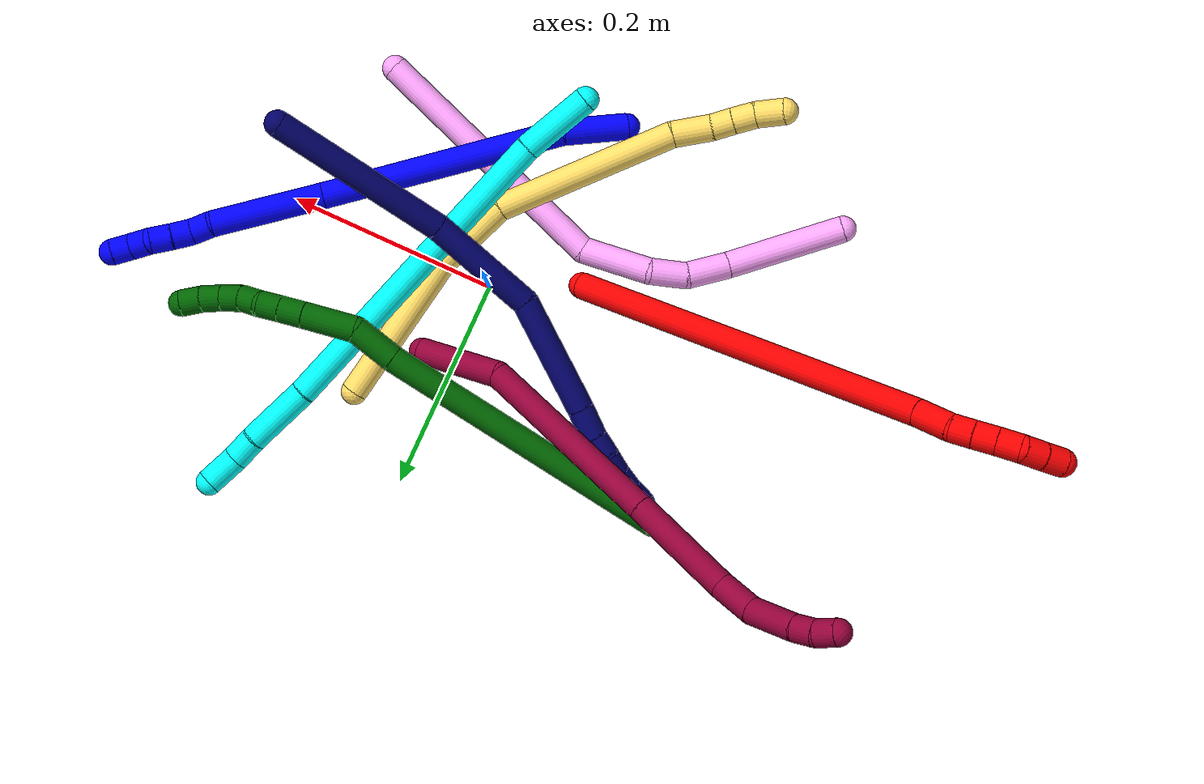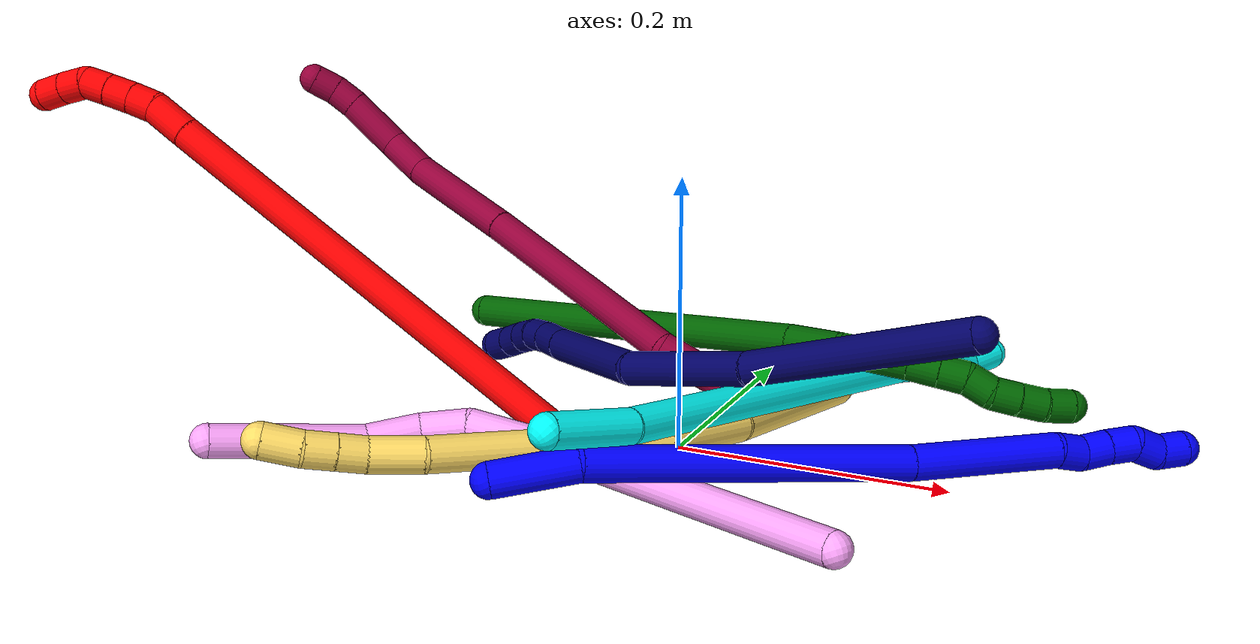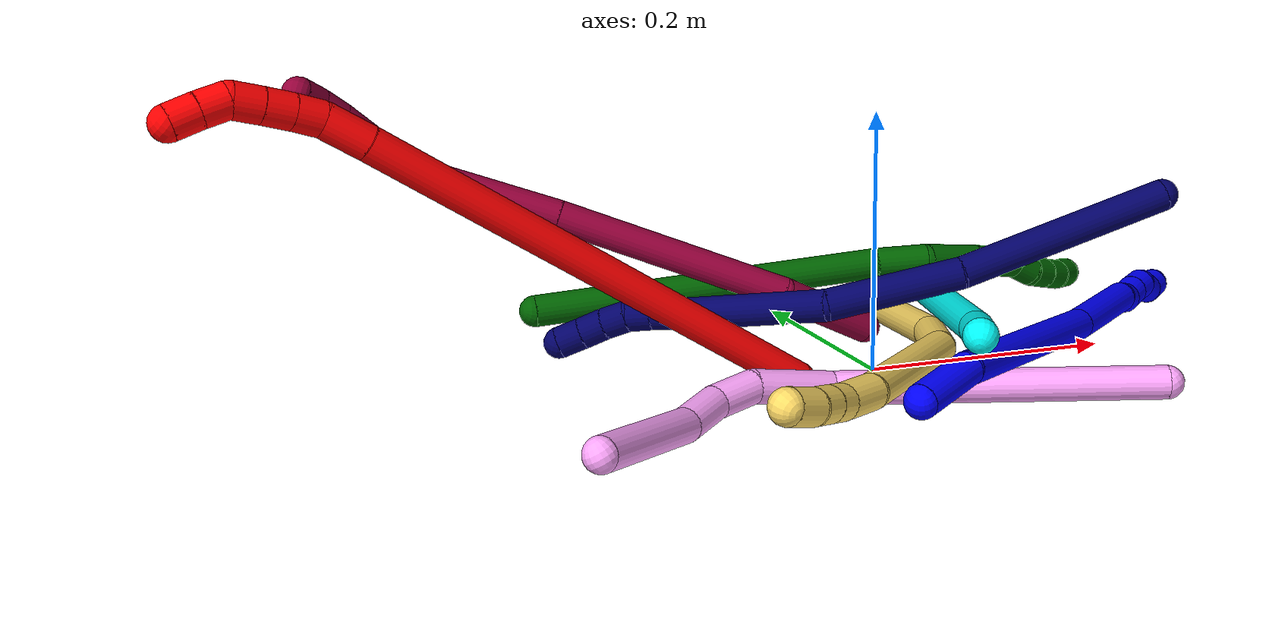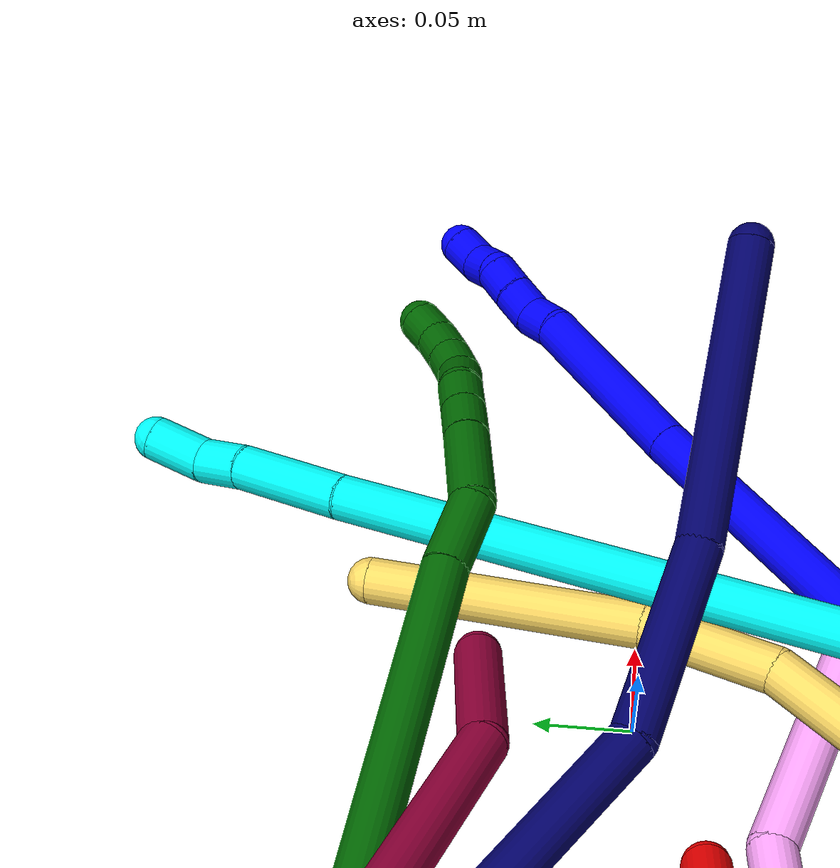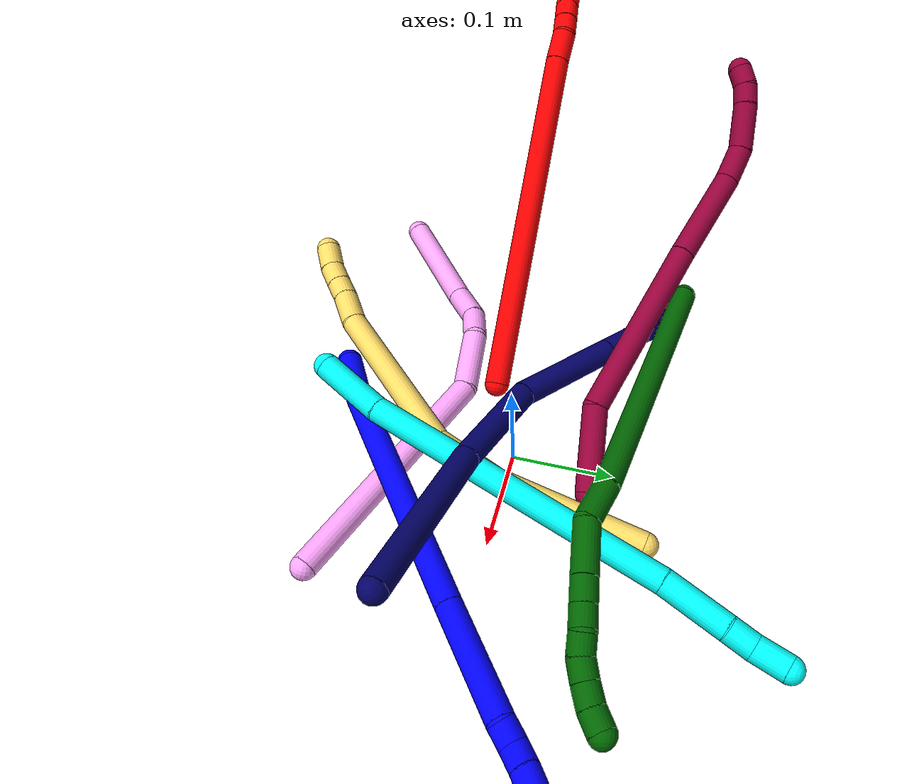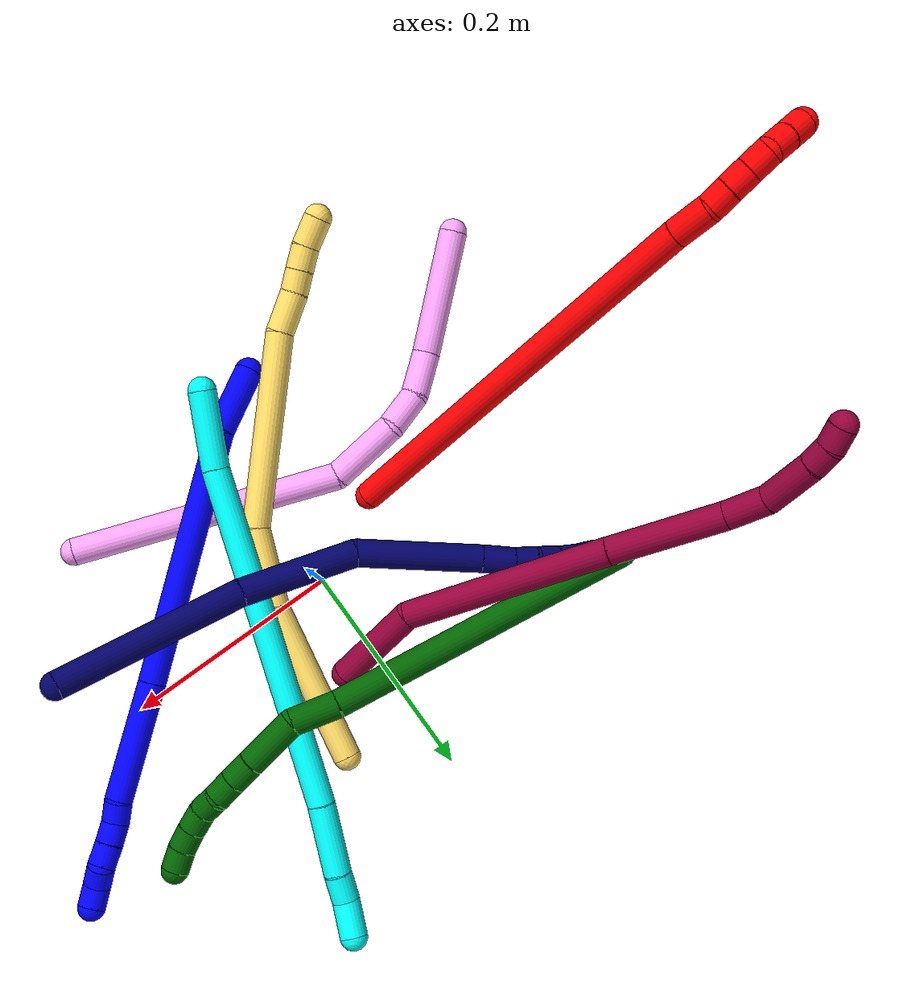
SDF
<sdf version="1.7">
 <world name="default">
  <plugin name="TubeGeneratorPlugin" filename="libtube_generator_plugin.so"/>
  <model name="photoneo_s_sensor">
   <static>1</static>
   <pose>0 0 2 1.57079 1.57079 3.14159</pose>
   <link name="link">
    <inertial><mass>0.1</mass></inertial>
    <sensor name="sensor" type="depth">
     <update_rate>30</update_rate>
     <camera>
      <horizontal_fov>1.22</horizontal_fov>
      <image><width>1920</width><height>1200</height><format>B8G8R8</format></image>
      <clip><near>0.1</near><far>4</far></clip>
      <depth_camera><output>points</output></depth_camera>
     </camera>
     <plugin name="camera_plugin" filename="libgazebo_ros_depth_camera.so">
      <baseline>0.2</baseline>
      <alwaysOn>1</alwaysOn>
      <updateRate>0.0</updateRate>
      <cameraName>camera_ir</cameraName>
      <imageTopicName>/camera/color/image_raw</imageTopicName>
      <cameraInfoTopicName>/camera/color/camera_info</cameraInfoTopicName>
      <depthImageTopicName>/camera/depth/image_raw</depthImageTopicName>
      <depthImageCameraInfoTopicName>/camera/depth/camera_info</depthImageCameraInfoTopicName>
      <pointCloudTopicName>/camera/depth/points</pointCloudTopicName>
      <frameName>fr_optical</frameName>
      <pointCloudCutoff>0.1</pointCloudCutoff>
      <pointCloudCutoffMax>2.0</pointCloudCutoffMax>
      <distortionK1>0</distortionK1>
      <distortionK2>0</distortionK2>
      <distortionK3>0</distortionK3>
      <distortionT1>0</distortionT1>
      <distortionT2>0</distortionT2>
      <CxPrime>0</CxPrime>
      <Cx>0</Cx>
      <Cy>0</Cy>
      <focalLength>0</focalLength>
      <hackBaseline>0</hackBaseline>
     </plugin>
    </sensor>
   </link>
  </model>
  <gravity>0 0 -9.8</gravity>
  <magnetic_field>6e-06 2.3e-05 -4.2e-05</magnetic_field>
  <atmosphere type="adiabatic"/>
  <physics name="default_physics" default="0" type="ode">
   <max_step_size>0.003</max_step_size>
   <real_time_factor>1</real_time_factor>
   <real_time_update_rate>1000</real_time_update_rate>
   <max_contacts>10000</max_contacts>
   <ode>
    <solver>
     <type>quick</type>
     <iters>100</iters>
     <sor>1.3</sor>
     <use_dynamic_moi_rescaling>0</use_dynamic_moi_rescaling>
    </solver>
    <constraints>
     <contact_max_correcting_vel>0</contact_max_correcting_vel>
     <contact_surface_layer>0.001</contact_surface_layer>
     <cfm>0</cfm>
     <erp>0.2</erp>
    </constraints>
   </ode>
  </physics>
  <scene><ambient>0.4 0.4 0.4 1</ambient><background>0.7 0.7 0.7 1</background><shadows>0</shadows></scene>
  <audio><device>default</device></audio>
  <spherical_coordinates>
   <surface_model>EARTH_WGS84</surface_model>
   <latitude_deg>0</latitude_deg>
   <longitude_deg>0</longitude_deg>
   <elevation>0</elevation>
   <heading_deg>0</heading_deg>
  </spherical_coordinates>
  <model name="bin">
   <static>1</static>
   <link name="bottom">
    <collision name="collision-bottom">
     <pose>0 0 -0.01 0 -0 0</pose>
     <geometry><box><size>0.8 0.6 0.02</size></box></geometry>
     <surface>
      <friction><ode><mu>100</mu><mu2>100</mu2></ode></friction>
      <contact><collide_bitmask>65535</collide_bitmask></contact>
     </surface>
    </collision>
   </link>
   <link name="west_wall">
    <collision name="collision-west_wall">
     <pose>-0.41 0 0.1 0 -0 0</pose>
     <geometry><box><size>0.02 0.6 0.2</size></box></geometry>
     <surface>
      <friction><ode><mu>100</mu><mu2>100</mu2></ode></friction>
      <contact><collide_bitmask>65535</collide_bitmask></contact>
     </surface>
    </collision>
   </link>
   <link name="east_wall">
    <collision name="collision-east_wall">
     <pose>0.41 0 0.1 0 -0 0</pose>
     <geometry><box><size>0.02 0.6 0.2</size></box></geometry>
     <surface>
      <friction><ode><mu>100</mu><mu2>100</mu2></ode></friction>
      <contact><collide_bitmask>65535</collide_bitmask></contact>
     </surface>
    </collision>
   </link>
   <link name="south_wall">
    <collision name="collision-south_wall">
     <pose>0 -0.31 0.1 0 -0 0</pose>
     <geometry><box><size>0.8 0.02 0.2</size></box></geometry>
     <surface>
      <friction><ode><mu>100</mu><mu2>100</mu2></ode></friction>
      <contact><collide_bitmask>65535</collide_bitmask></contact>
     </surface>
    </collision>
   </link>
   <link name="north_wall">
    <collision name="collision-north_wall">
     <pose>0 0.31 0.1 0 -0 0</pose>
     <geometry><box><size>0.8 0.02 0.2</size></box></geometry>
     <surface>
      <friction><ode><mu>100</mu><mu2>100</mu2></ode></friction>
      <contact><collide_bitmask>65535</collide_bitmask></contact>
     </surface>
    </collision>
   </link>
  </model>
  <model name="1">
   <static>0</static>
   <link name="1">
    <collision name="collision-cylinder-e_1_1_4">
     <pose>0.027719 0.004059 0.011163 -0.348718 1.16595 -0.231276</pose>
     <geometry><cylinder><radius>0.0125</radius><length>0.060314</length></cylinder></geometry>
     <surface>
      <friction><ode><mu>1.16</mu><mu2>1.16</mu2><slip1>0</slip1><slip2>0</slip2></ode></friction>
      <contact><ode><kp>1e+06</kp><kd>1</kd><max_vel>0</max_vel><min_depth>0.001</min_depth></ode></contact>
     </surface>
    </collision>
    <visual name="visual-cylinder-e_1_1_4">
     <pose>0.027719 0.004059 0.011163 -0.348718 1.16595 -0.231276</pose>
     <geometry><cylinder><radius>0.0125</radius><length>0.060314</length></cylinder></geometry>
     <material><ambient>0 0 1 1</ambient></material>
    </visual>
    <collision name="collision-cylinder-e_2_4_5">
     <pose>0.147286 0.014483 0.092315 -0.090705 0.917672 -0.044832</pose>
     <geometry><cylinder><radius>0.0125</radius><length>0.2313</length></cylinder></geometry>
     <surface>
      <friction><ode><mu>1.16</mu><mu2>1.16</mu2><slip1>0</slip1><slip2>0</slip2></ode></friction>
      <contact><ode><kp>1e+06</kp><kd>1</kd><max_vel>0</max_vel><min_depth>0.001</min_depth></ode></contact>
     </surface>
    </collision>
    <visual name="visual-cylinder-e_2_4_5">
     <pose>0.147286 0.014483 0.092315 -0.090705 0.917672 -0.044832</pose>
     <geometry><cylinder><radius>0.0125</radius><length>0.2313</length></cylinder></geometry>
     <material><ambient>0 0 1 1</ambient></material>
    </visual>
    <collision name="collision-cylinder-e_3_5_6">
     <pose>0.284541 0.022809 0.191206 -0.067696 1.0029 -0.03712</pose>
     <geometry><cylinder><radius>0.0125</radius><length>0.107721</length></cylinder></geometry>
     <surface>
      <friction><ode><mu>1.16</mu><mu2>1.16</mu2><slip1>0</slip1><slip2>0</slip2></ode></friction>
      <contact><ode><kp>1e+06</kp><kd>1</kd><max_vel>0</max_vel><min_depth>0.001</min_depth></ode></contact>
     </surface>
    </collision>
    <visual name="visual-cylinder-e_3_5_6">
     <pose>0.284541 0.022809 0.191206 -0.067696 1.0029 -0.03712</pose>
     <geometry><cylinder><radius>0.0125</radius><length>0.107721</length></cylinder></geometry>
     <material><ambient>0 0 1 1</ambient></material>
    </visual>
    <collision name="collision-cylinder-e_4_6_7">
     <pose>0.336863 0.024677 0.227555 0.012235 0.74851 0.004805</pose>
     <geometry><cylinder><radius>0.0125</radius><length>0.020324</length></cylinder></geometry>
     <surface>
      <friction><ode><mu>1.16</mu><mu2>1.16</mu2><slip1>0</slip1><slip2>0</slip2></ode></friction>
      <contact><ode><kp>1e+06</kp><kd>1</kd><max_vel>0</max_vel><min_depth>0.001</min_depth></ode></contact>
     </surface>
    </collision>
    <visual name="visual-cylinder-e_4_6_7">
     <pose>0.336863 0.024677 0.227555 0.012235 0.74851 0.004805</pose>
     <geometry><cylinder><radius>0.0125</radius><length>0.020324</length></cylinder></geometry>
     <material><ambient>0 0 1 1</ambient></material>
    </visual>
    <collision name="collision-cylinder-e_5_7_8">
     <pose>0.352889 0.02457 0.239298 0.003776 1.12998 0.002394</pose>
     <geometry><cylinder><radius>0.0125</radius><length>0.020146</length></cylinder></geometry>
     <surface>
      <friction><ode><mu>1.16</mu><mu2>1.16</mu2><slip1>0</slip1><slip2>0</slip2></ode></friction>
      <contact><ode><kp>1e+06</kp><kd>1</kd><max_vel>0</max_vel><min_depth>0.001</min_depth></ode></contact>
     </surface>
    </collision>
    <visual name="visual-cylinder-e_5_7_8">
     <pose>0.352889 0.02457 0.239298 0.003776 1.12998 0.002394</pose>
     <geometry><cylinder><radius>0.0125</radius><length>0.020146</length></cylinder></geometry>
     <material><ambient>0 0 1 1</ambient></material>
    </visual>
    <collision name="collision-cylinder-e_6_8_9">
     <pose>0.370919 0.025174 0.248194 -0.134042 1.09112 -0.081442</pose>
     <geometry><cylinder><radius>0.0125</radius><length>0.020109</length></cylinder></geometry>
     <surface>
      <friction><ode><mu>1.16</mu><mu2>1.16</mu2><slip1>0</slip1><slip2>0</slip2></ode></friction>
      <contact><ode><kp>1e+06</kp><kd>1</kd><max_vel>0</max_vel><min_depth>0.001</min_depth></ode></contact>
     </surface>
    </collision>
    <visual name="visual-cylinder-e_6_8_9">
     <pose>0.370919 0.025174 0.248194 -0.134042 1.09112 -0.081442</pose>
     <geometry><cylinder><radius>0.0125</radius><length>0.020109</length></cylinder></geometry>
     <material><ambient>0 0 1 1</ambient></material>
    </visual>
    <collision name="collision-cylinder-e_7_9_10">
     <pose>0.385467 0.027155 0.260989 -0.164534 0.59539 -0.050584</pose>
     <geometry><cylinder><radius>0.0125</radius><length>0.02007</length></cylinder></geometry>
     <surface>
      <friction><ode><mu>1.16</mu><mu2>1.16</mu2><slip1>0</slip1><slip2>0</slip2></ode></friction>
      <contact><ode><kp>1e+06</kp><kd>1</kd><max_vel>0</max_vel><min_depth>0.001</min_depth></ode></contact>
     </surface>
    </collision>
    <visual name="visual-cylinder-e_7_9_10">
     <pose>0.385467 0.027155 0.260989 -0.164534 0.59539 -0.050584</pose>
     <geometry><cylinder><radius>0.0125</radius><length>0.02007</length></cylinder></geometry>
     <material><ambient>0 0 1 1</ambient></material>
    </visual>
    <collision name="collision-cylinder-e_8_10_2">
     <pose>0.399667 0.028438 0.274349 0.014942 1.02858 0.008442</pose>
     <geometry><cylinder><radius>0.0125</radius><length>0.020015</length></cylinder></geometry>
     <surface>
      <friction><ode><mu>1.16</mu><mu2>1.16</mu2><slip1>0</slip1><slip2>0</slip2></ode></friction>
      <contact><ode><kp>1e+06</kp><kd>1</kd><max_vel>0</max_vel><min_depth>0.001</min_depth></ode></contact>
     </surface>
    </collision>
    <visual name="visual-cylinder-e_8_10_2">
     <pose>0.399667 0.028438 0.274349 0.014942 1.02858 0.008442</pose>
     <geometry><cylinder><radius>0.0125</radius><length>0.020015</length></cylinder></geometry>
     <material><ambient>0 0 1 1</ambient></material>
    </visual>
    <collision name="collision-sphere-2">
     <pose>0.408239 0.028361 0.279512 0 -0 0</pose>
     <geometry><sphere><radius>0.0125</radius></sphere></geometry>
     <surface>
      <friction><ode><mu>1.16</mu><mu2>1.16</mu2><slip1>0</slip1><slip2>0</slip2></ode></friction>
      <contact><ode><kp>1e+06</kp><kd>1</kd><max_vel>0</max_vel><min_depth>0.001</min_depth></ode></contact>
     </surface>
    </collision>
    <visual name="visual-sphere-2">
     <pose>0.408239 0.028361 0.279512 0 -0 0</pose>
     <geometry><sphere><radius>0.0125</radius></sphere></geometry>
     <material><ambient>0 0 1 1</ambient></material>
    </visual>
    <collision name="collision-sphere-10">
     <pose>0.391095 0.028516 0.269185 0 -0 0</pose>
     <geometry><sphere><radius>0.0125</radius></sphere></geometry>
     <surface>
      <friction><ode><mu>1.16</mu><mu2>1.16</mu2><slip1>0</slip1><slip2>0</slip2></ode></friction>
      <contact><ode><kp>1e+06</kp><kd>1</kd><max_vel>0</max_vel><min_depth>0.001</min_depth></ode></contact>
     </surface>
    </collision>
    <visual name="visual-sphere-10">
     <pose>0.391095 0.028516 0.269185 0 -0 0</pose>
     <geometry><sphere><radius>0.0125</radius></sphere></geometry>
     <material><ambient>0 0 1 1</ambient></material>
    </visual>
    <collision name="collision-sphere-9">
     <pose>0.379839 0.025794 0.252793 0 -0 0</pose>
     <geometry><sphere><radius>0.0125</radius></sphere></geometry>
     <surface>
      <friction><ode><mu>1.16</mu><mu2>1.16</mu2><slip1>0</slip1><slip2>0</slip2></ode></friction>
      <contact><ode><kp>1e+06</kp><kd>1</kd><max_vel>0</max_vel><min_depth>0.001</min_depth></ode></contact>
     </surface>
    </collision>
    <visual name="visual-sphere-9">
     <pose>0.379839 0.025794 0.252793 0 -0 0</pose>
     <geometry><sphere><radius>0.0125</radius></sphere></geometry>
     <material><ambient>0 0 1 1</ambient></material>
    </visual>
    <collision name="collision-sphere-4">
     <pose>0.055438 0.008117 0.022327 0 -0 0</pose>
     <geometry><sphere><radius>0.0125</radius></sphere></geometry>
     <surface>
      <friction><ode><mu>1.16</mu><mu2>1.16</mu2><slip1>0</slip1><slip2>0</slip2></ode></friction>
      <contact><ode><kp>1e+06</kp><kd>1</kd><max_vel>0</max_vel><min_depth>0.001</min_depth></ode></contact>
     </surface>
    </collision>
    <visual name="visual-sphere-4">
     <pose>0.055438 0.008117 0.022327 0 -0 0</pose>
     <geometry><sphere><radius>0.0125</radius></sphere></geometry>
     <material><ambient>0 0 1 1</ambient></material>
    </visual>
    <collision name="collision-sphere-1">
     <geometry><sphere><radius>0.0125</radius></sphere></geometry>
     <surface>
      <friction><ode><mu>1.16</mu><mu2>1.16</mu2><slip1>0</slip1><slip2>0</slip2></ode></friction>
      <contact><ode><kp>1e+06</kp><kd>1</kd><max_vel>0</max_vel><min_depth>0.001</min_depth></ode></contact>
     </surface>
    </collision>
    <visual name="visual-sphere-1">
     <geometry><sphere><radius>0.0125</radius></sphere></geometry>
     <material><ambient>0 0 1 1</ambient></material>
    </visual>
    <collision name="collision-sphere-8">
     <pose>0.361999 0.024554 0.243596 0 -0 0</pose>
     <geometry><sphere><radius>0.0125</radius></sphere></geometry>
     <surface>
      <friction><ode><mu>1.16</mu><mu2>1.16</mu2><slip1>0</slip1><slip2>0</slip2></ode></friction>
      <contact><ode><kp>1e+06</kp><kd>1</kd><max_vel>0</max_vel><min_depth>0.001</min_depth></ode></contact>
     </surface>
    </collision>
    <visual name="visual-sphere-8">
     <pose>0.361999 0.024554 0.243596 0 -0 0</pose>
     <geometry><sphere><radius>0.0125</radius></sphere></geometry>
     <material><ambient>0 0 1 1</ambient></material>
    </visual>
    <collision name="collision-sphere-5">
     <pose>0.239134 0.020849 0.162303 0 -0 0</pose>
     <geometry><sphere><radius>0.0125</radius></sphere></geometry>
     <surface>
      <friction><ode><mu>1.16</mu><mu2>1.16</mu2><slip1>0</slip1><slip2>0</slip2></ode></friction>
      <contact><ode><kp>1e+06</kp><kd>1</kd><max_vel>0</max_vel><min_depth>0.001</min_depth></ode></contact>
     </surface>
    </collision>
    <visual name="visual-sphere-5">
     <pose>0.239134 0.020849 0.162303 0 -0 0</pose>
     <geometry><sphere><radius>0.0125</radius></sphere></geometry>
     <material><ambient>0 0 1 1</ambient></material>
    </visual>
    <collision name="collision-sphere-6">
     <pose>0.329947 0.024768 0.220109 0 -0 0</pose>
     <geometry><sphere><radius>0.0125</radius></sphere></geometry>
     <surface>
      <friction><ode><mu>1.16</mu><mu2>1.16</mu2><slip1>0</slip1><slip2>0</slip2></ode></friction>
      <contact><ode><kp>1e+06</kp><kd>1</kd><max_vel>0</max_vel><min_depth>0.001</min_depth></ode></contact>
     </surface>
    </collision>
    <visual name="visual-sphere-6">
     <pose>0.329947 0.024768 0.220109 0 -0 0</pose>
     <geometry><sphere><radius>0.0125</radius></sphere></geometry>
     <material><ambient>0 0 1 1</ambient></material>
    </visual>
    <collision name="collision-sphere-7">
     <pose>0.343779 0.024586 0.235 0 -0 0</pose>
     <geometry><sphere><radius>0.0125</radius></sphere></geometry>
     <surface>
      <friction><ode><mu>1.16</mu><mu2>1.16</mu2><slip1>0</slip1><slip2>0</slip2></ode></friction>
      <contact><ode><kp>1e+06</kp><kd>1</kd><max_vel>0</max_vel><min_depth>0.001</min_depth></ode></contact>
     </surface>
    </collision>
    <visual name="visual-sphere-7">
     <pose>0.343779 0.024586 0.235 0 -0 0</pose>
     <geometry><sphere><radius>0.0125</radius></sphere></geometry>
     <material><ambient>0 0 1 1</ambient></material>
    </visual>
    <inertial>
     <pose>0.207081 0.017337 0.135577 0 -0 0</pose>
     <mass>0.5</mass>
     <inertia>
      <ixx>0.000701</ixx>
      <ixy>0</ixy>
      <ixz>0</ixz>
      <iyy>0.001144</iyy>
      <iyz>0</iyz>
      <izz>-0.000985</izz>
     </inertia>
    </inertial>
   </link>
   <pose>-0.055217 -0.187703 0.033776 -2.88548 -0.555201 0.57735</pose>
  </model>
  <model name="2">
   <static>0</static>
   <link name="2">
    <collision name="collision-cylinder-e_1_1_4">
     <pose>-0.018282 0.003272 0.181965 -0.017981 -0.100117 0.000901</pose>
     <geometry><cylinder><radius>0.0125</radius><length>0.36582</length></cylinder></geometry>
     <surface>
      <friction><ode><mu>1.16</mu><mu2>1.16</mu2><slip1>0</slip1><slip2>0</slip2></ode></friction>
      <contact><ode><kp>1e+06</kp><kd>1</kd><max_vel>0</max_vel><min_depth>0.001</min_depth></ode></contact>
     </surface>
    </collision>
    <visual name="visual-cylinder-e_1_1_4">
     <pose>-0.018282 0.003272 0.181965 -0.017981 -0.100117 0.000901</pose>
     <geometry><cylinder><radius>0.0125</radius><length>0.36582</length></cylinder></geometry>
     <material><ambient>1 0 0 1</ambient></material>
    </visual>
    <collision name="collision-cylinder-e_2_4_5">
     <pose>-0.038171 0.00784 0.380282 -0.079073 -0.097655 0.003866</pose>
     <geometry><cylinder><radius>0.0125</radius><length>0.032965</length></cylinder></geometry>
     <surface>
      <friction><ode><mu>1.16</mu><mu2>1.16</mu2><slip1>0</slip1><slip2>0</slip2></ode></friction>
      <contact><ode><kp>1e+06</kp><kd>1</kd><max_vel>0</max_vel><min_depth>0.001</min_depth></ode></contact>
     </surface>
    </collision>
    <visual name="visual-cylinder-e_2_4_5">
     <pose>-0.038171 0.00784 0.380282 -0.079073 -0.097655 0.003866</pose>
     <geometry><cylinder><radius>0.0125</radius><length>0.032965</length></cylinder></geometry>
     <material><ambient>1 0 0 1</ambient></material>
    </visual>
    <collision name="collision-cylinder-e_3_5_6">
     <pose>-0.043397 0.00937 0.406021 -0.024933 -0.367938 0.00464</pose>
     <geometry><cylinder><radius>0.0125</radius><length>0.020126</length></cylinder></geometry>
     <surface>
      <friction><ode><mu>1.16</mu><mu2>1.16</mu2><slip1>0</slip1><slip2>0</slip2></ode></friction>
      <contact><ode><kp>1e+06</kp><kd>1</kd><max_vel>0</max_vel><min_depth>0.001</min_depth></ode></contact>
     </surface>
    </collision>
    <visual name="visual-cylinder-e_3_5_6">
     <pose>-0.043397 0.00937 0.406021 -0.024933 -0.367938 0.00464</pose>
     <geometry><cylinder><radius>0.0125</radius><length>0.020126</length></cylinder></geometry>
     <material><ambient>1 0 0 1</ambient></material>
    </visual>
    <collision name="collision-cylinder-e_4_6_7">
     <pose>-0.0511 0.009895 0.42474 -0.031152 -0.412213 0.006514</pose>
     <geometry><cylinder><radius>0.0125</radius><length>0.020381</length></cylinder></geometry>
     <surface>
      <friction><ode><mu>1.16</mu><mu2>1.16</mu2><slip1>0</slip1><slip2>0</slip2></ode></friction>
      <contact><ode><kp>1e+06</kp><kd>1</kd><max_vel>0</max_vel><min_depth>0.001</min_depth></ode></contact>
     </surface>
    </collision>
    <visual name="visual-cylinder-e_4_6_7">
     <pose>-0.0511 0.009895 0.42474 -0.031152 -0.412213 0.006514</pose>
     <geometry><cylinder><radius>0.0125</radius><length>0.020381</length></cylinder></geometry>
     <material><ambient>1 0 0 1</ambient></material>
    </visual>
    <collision name="collision-cylinder-e_5_7_8">
     <pose>-0.059453 0.010753 0.443465 -0.060368 -0.426125 0.013064</pose>
     <geometry><cylinder><radius>0.0125</radius><length>0.020666</length></cylinder></geometry>
     <surface>
      <friction><ode><mu>1.16</mu><mu2>1.16</mu2><slip1>0</slip1><slip2>0</slip2></ode></friction>
      <contact><ode><kp>1e+06</kp><kd>1</kd><max_vel>0</max_vel><min_depth>0.001</min_depth></ode></contact>
     </surface>
    </collision>
    <visual name="visual-cylinder-e_5_7_8">
     <pose>-0.059453 0.010753 0.443465 -0.060368 -0.426125 0.013064</pose>
     <geometry><cylinder><radius>0.0125</radius><length>0.020666</length></cylinder></geometry>
     <material><ambient>1 0 0 1</ambient></material>
    </visual>
    <collision name="collision-cylinder-e_6_8_9">
     <pose>-0.071543 0.01351 0.458719 -0.357339 -0.895805 0.173108</pose>
     <geometry><cylinder><radius>0.0125</radius><length>0.020028</length></cylinder></geometry>
     <surface>
      <friction><ode><mu>1.16</mu><mu2>1.16</mu2><slip1>0</slip1><slip2>0</slip2></ode></friction>
      <contact><ode><kp>1e+06</kp><kd>1</kd><max_vel>0</max_vel><min_depth>0.001</min_depth></ode></contact>
     </surface>
    </collision>
    <visual name="visual-cylinder-e_6_8_9">
     <pose>-0.071543 0.01351 0.458719 -0.357339 -0.895805 0.173108</pose>
     <geometry><cylinder><radius>0.0125</radius><length>0.020028</length></cylinder></geometry>
     <material><ambient>1 0 0 1</ambient></material>
    </visual>
    <collision name="collision-cylinder-e_7_9_2">
     <pose>-0.087504 0.017885 0.469971 -0.385324 -0.950615 0.200131</pose>
     <geometry><cylinder><radius>0.0125</radius><length>0.020014</length></cylinder></geometry>
     <surface>
      <friction><ode><mu>1.16</mu><mu2>1.16</mu2><slip1>0</slip1><slip2>0</slip2></ode></friction>
      <contact><ode><kp>1e+06</kp><kd>1</kd><max_vel>0</max_vel><min_depth>0.001</min_depth></ode></contact>
     </surface>
    </collision>
    <visual name="visual-cylinder-e_7_9_2">
     <pose>-0.087504 0.017885 0.469971 -0.385324 -0.950615 0.200131</pose>
     <geometry><cylinder><radius>0.0125</radius><length>0.020014</length></cylinder></geometry>
     <material><ambient>1 0 0 1</ambient></material>
    </visual>
    <collision name="collision-sphere-2">
     <pose>-0.095647 0.020071 0.47536 0 -0 0</pose>
     <geometry><sphere><radius>0.0125</radius></sphere></geometry>
     <surface>
      <friction><ode><mu>1.16</mu><mu2>1.16</mu2><slip1>0</slip1><slip2>0</slip2></ode></friction>
      <contact><ode><kp>1e+06</kp><kd>1</kd><max_vel>0</max_vel><min_depth>0.001</min_depth></ode></contact>
     </surface>
    </collision>
    <visual name="visual-sphere-2">
     <pose>-0.095647 0.020071 0.47536 0 -0 0</pose>
     <geometry><sphere><radius>0.0125</radius></sphere></geometry>
     <material><ambient>1 0 0 1</ambient></material>
    </visual>
    <collision name="collision-sphere-9">
     <pose>-0.079361 0.015699 0.464581 0 -0 0</pose>
     <geometry><sphere><radius>0.0125</radius></sphere></geometry>
     <surface>
      <friction><ode><mu>1.16</mu><mu2>1.16</mu2><slip1>0</slip1><slip2>0</slip2></ode></friction>
      <contact><ode><kp>1e+06</kp><kd>1</kd><max_vel>0</max_vel><min_depth>0.001</min_depth></ode></contact>
     </surface>
    </collision>
    <visual name="visual-sphere-9">
     <pose>-0.079361 0.015699 0.464581 0 -0 0</pose>
     <geometry><sphere><radius>0.0125</radius></sphere></geometry>
     <material><ambient>1 0 0 1</ambient></material>
    </visual>
    <collision name="collision-sphere-4">
     <pose>-0.036564 0.006544 0.36393 0 -0 0</pose>
     <geometry><sphere><radius>0.0125</radius></sphere></geometry>
     <surface>
      <friction><ode><mu>1.16</mu><mu2>1.16</mu2><slip1>0</slip1><slip2>0</slip2></ode></friction>
      <contact><ode><kp>1e+06</kp><kd>1</kd><max_vel>0</max_vel><min_depth>0.001</min_depth></ode></contact>
     </surface>
    </collision>
    <visual name="visual-sphere-4">
     <pose>-0.036564 0.006544 0.36393 0 -0 0</pose>
     <geometry><sphere><radius>0.0125</radius></sphere></geometry>
     <material><ambient>1 0 0 1</ambient></material>
    </visual>
    <collision name="collision-sphere-1">
     <geometry><sphere><radius>0.0125</radius></sphere></geometry>
     <surface>
      <friction><ode><mu>1.16</mu><mu2>1.16</mu2><slip1>0</slip1><slip2>0</slip2></ode></friction>
      <contact><ode><kp>1e+06</kp><kd>1</kd><max_vel>0</max_vel><min_depth>0.001</min_depth></ode></contact>
     </surface>
    </collision>
    <visual name="visual-sphere-1">
     <geometry><sphere><radius>0.0125</radius></sphere></geometry>
     <material><ambient>1 0 0 1</ambient></material>
    </visual>
    <collision name="collision-sphere-8">
     <pose>-0.063725 0.011321 0.452856 0 -0 0</pose>
     <geometry><sphere><radius>0.0125</radius></sphere></geometry>
     <surface>
      <friction><ode><mu>1.16</mu><mu2>1.16</mu2><slip1>0</slip1><slip2>0</slip2></ode></friction>
      <contact><ode><kp>1e+06</kp><kd>1</kd><max_vel>0</max_vel><min_depth>0.001</min_depth></ode></contact>
     </surface>
    </collision>
    <visual name="visual-sphere-8">
     <pose>-0.063725 0.011321 0.452856 0 -0 0</pose>
     <geometry><sphere><radius>0.0125</radius></sphere></geometry>
     <material><ambient>1 0 0 1</ambient></material>
    </visual>
    <collision name="collision-sphere-5">
     <pose>-0.039778 0.009136 0.396635 0 -0 0</pose>
     <geometry><sphere><radius>0.0125</radius></sphere></geometry>
     <surface>
      <friction><ode><mu>1.16</mu><mu2>1.16</mu2><slip1>0</slip1><slip2>0</slip2></ode></friction>
      <contact><ode><kp>1e+06</kp><kd>1</kd><max_vel>0</max_vel><min_depth>0.001</min_depth></ode></contact>
     </surface>
    </collision>
    <visual name="visual-sphere-5">
     <pose>-0.039778 0.009136 0.396635 0 -0 0</pose>
     <geometry><sphere><radius>0.0125</radius></sphere></geometry>
     <material><ambient>1 0 0 1</ambient></material>
    </visual>
    <collision name="collision-sphere-6">
     <pose>-0.047017 0.009604 0.415408 0 -0 0</pose>
     <geometry><sphere><radius>0.0125</radius></sphere></geometry>
     <surface>
      <friction><ode><mu>1.16</mu><mu2>1.16</mu2><slip1>0</slip1><slip2>0</slip2></ode></friction>
      <contact><ode><kp>1e+06</kp><kd>1</kd><max_vel>0</max_vel><min_depth>0.001</min_depth></ode></contact>
     </surface>
    </collision>
    <visual name="visual-sphere-6">
     <pose>-0.047017 0.009604 0.415408 0 -0 0</pose>
     <geometry><sphere><radius>0.0125</radius></sphere></geometry>
     <material><ambient>1 0 0 1</ambient></material>
    </visual>
    <collision name="collision-sphere-7">
     <pose>-0.055182 0.010186 0.434073 0 -0 0</pose>
     <geometry><sphere><radius>0.0125</radius></sphere></geometry>
     <surface>
      <friction><ode><mu>1.16</mu><mu2>1.16</mu2><slip1>0</slip1><slip2>0</slip2></ode></friction>
      <contact><ode><kp>1e+06</kp><kd>1</kd><max_vel>0</max_vel><min_depth>0.001</min_depth></ode></contact>
     </surface>
    </collision>
    <visual name="visual-sphere-7">
     <pose>-0.055182 0.010186 0.434073 0 -0 0</pose>
     <geometry><sphere><radius>0.0125</radius></sphere></geometry>
     <material><ambient>1 0 0 1</ambient></material>
    </visual>
    <inertial>
     <pose>-0.028548 0.005393 0.247377 0 -0 0</pose>
     <mass>0.5</mass>
     <inertia><ixx>0.00408</ixx><ixy>0</ixy><ixz>0</ixz><iyy>0.00411</iyy><iyz>0</iyz><izz>0.000376</izz></inertia>
    </inertial>
   </link>
   <pose>-0.078875 -0.037054 0.011521 -0.472237 -0.810084 0.609993</pose>
  </model>
  <model name="3">
   <static>0</static>
   <link name="3">
    <collision name="collision-cylinder-e_1_1_4">
     <pose>0.019154 0.011517 0.026436 -0.410863 0.586328 -0.125633</pose>
     <geometry><cylinder><radius>0.0125</radius><length>0.069235</length></cylinder></geometry>
     <surface>
      <friction><ode><mu>1.16</mu><mu2>1.16</mu2><slip1>0</slip1><slip2>0</slip2></ode></friction>
      <contact><ode><kp>1e+06</kp><kd>1</kd><max_vel>0</max_vel><min_depth>0.001</min_depth></ode></contact>
     </surface>
    </collision>
    <visual name="visual-cylinder-e_1_1_4">
     <pose>0.019154 0.011517 0.026436 -0.410863 0.586328 -0.125633</pose>
     <geometry><cylinder><radius>0.0125</radius><length>0.069235</length></cylinder></geometry>
     <material><ambient>0.003922 1 0.996078 1</ambient></material>
    </visual>
    <collision name="collision-cylinder-e_2_4_5">
     <pose>0.105212 0.090027 0.174017 -0.505145 0.450187 -0.118052</pose>
     <geometry><cylinder><radius>0.0125</radius><length>0.307509</length></cylinder></geometry>
     <surface>
      <friction><ode><mu>1.16</mu><mu2>1.16</mu2><slip1>0</slip1><slip2>0</slip2></ode></friction>
      <contact><ode><kp>1e+06</kp><kd>1</kd><max_vel>0</max_vel><min_depth>0.001</min_depth></ode></contact>
     </surface>
    </collision>
    <visual name="visual-cylinder-e_2_4_5">
     <pose>0.105212 0.090027 0.174017 -0.505145 0.450187 -0.118052</pose>
     <geometry><cylinder><radius>0.0125</radius><length>0.307509</length></cylinder></geometry>
     <material><ambient>0.003922 1 0.996078 1</ambient></material>
    </visual>
    <collision name="collision-cylinder-e_3_5_6">
     <pose>0.188423 0.16937 0.319736 -0.465666 0.535229 -0.129857</pose>
     <geometry><cylinder><radius>0.0125</radius><length>0.063949</length></cylinder></geometry>
     <surface>
      <friction><ode><mu>1.16</mu><mu2>1.16</mu2><slip1>0</slip1><slip2>0</slip2></ode></friction>
      <contact><ode><kp>1e+06</kp><kd>1</kd><max_vel>0</max_vel><min_depth>0.001</min_depth></ode></contact>
     </surface>
    </collision>
    <visual name="visual-cylinder-e_3_5_6">
     <pose>0.188423 0.16937 0.319736 -0.465666 0.535229 -0.129857</pose>
     <geometry><cylinder><radius>0.0125</radius><length>0.063949</length></cylinder></geometry>
     <material><ambient>0.003922 1 0.996078 1</ambient></material>
    </visual>
    <collision name="collision-cylinder-e_4_6_7">
     <pose>0.212153 0.187825 0.353411 -0.590935 0.595247 -0.186186</pose>
     <geometry><cylinder><radius>0.0125</radius><length>0.026471</length></cylinder></geometry>
     <surface>
      <friction><ode><mu>1.16</mu><mu2>1.16</mu2><slip1>0</slip1><slip2>0</slip2></ode></friction>
      <contact><ode><kp>1e+06</kp><kd>1</kd><max_vel>0</max_vel><min_depth>0.001</min_depth></ode></contact>
     </surface>
    </collision>
    <visual name="visual-cylinder-e_4_6_7">
     <pose>0.212153 0.187825 0.353411 -0.590935 0.595247 -0.186186</pose>
     <geometry><cylinder><radius>0.0125</radius><length>0.026471</length></cylinder></geometry>
     <material><ambient>0.003922 1 0.996078 1</ambient></material>
    </visual>
    <collision name="collision-cylinder-e_5_7_2">
     <pose>0.225469 0.199121 0.37693 -0.34549 0.367201 -0.064778</pose>
     <geometry><cylinder><radius>0.0125</radius><length>0.032837</length></cylinder></geometry>
     <surface>
      <friction><ode><mu>1.16</mu><mu2>1.16</mu2><slip1>0</slip1><slip2>0</slip2></ode></friction>
      <contact><ode><kp>1e+06</kp><kd>1</kd><max_vel>0</max_vel><min_depth>0.001</min_depth></ode></contact>
     </surface>
    </collision>
    <visual name="visual-cylinder-e_5_7_2">
     <pose>0.225469 0.199121 0.37693 -0.34549 0.367201 -0.064778</pose>
     <geometry><cylinder><radius>0.0125</radius><length>0.032837</length></cylinder></geometry>
     <material><ambient>0.003922 1 0.996078 1</ambient></material>
    </visual>
    <collision name="collision-sphere-2">
     <pose>0.231363 0.20431 0.391349 0 -0 0</pose>
     <geometry><sphere><radius>0.0125</radius></sphere></geometry>
     <surface>
      <friction><ode><mu>1.16</mu><mu2>1.16</mu2><slip1>0</slip1><slip2>0</slip2></ode></friction>
      <contact><ode><kp>1e+06</kp><kd>1</kd><max_vel>0</max_vel><min_depth>0.001</min_depth></ode></contact>
     </surface>
    </collision>
    <visual name="visual-sphere-2">
     <pose>0.231363 0.20431 0.391349 0 -0 0</pose>
     <geometry><sphere><radius>0.0125</radius></sphere></geometry>
     <material><ambient>0.003922 1 0.996078 1</ambient></material>
    </visual>
    <collision name="collision-sphere-7">
     <pose>0.219574 0.193931 0.362512 0 -0 0</pose>
     <geometry><sphere><radius>0.0125</radius></sphere></geometry>
     <surface>
      <friction><ode><mu>1.16</mu><mu2>1.16</mu2><slip1>0</slip1><slip2>0</slip2></ode></friction>
      <contact><ode><kp>1e+06</kp><kd>1</kd><max_vel>0</max_vel><min_depth>0.001</min_depth></ode></contact>
     </surface>
    </collision>
    <visual name="visual-sphere-7">
     <pose>0.219574 0.193931 0.362512 0 -0 0</pose>
     <geometry><sphere><radius>0.0125</radius></sphere></geometry>
     <material><ambient>0.003922 1 0.996078 1</ambient></material>
    </visual>
    <collision name="collision-sphere-6">
     <pose>0.204732 0.181719 0.34431 0 -0 0</pose>
     <geometry><sphere><radius>0.0125</radius></sphere></geometry>
     <surface>
      <friction><ode><mu>1.16</mu><mu2>1.16</mu2><slip1>0</slip1><slip2>0</slip2></ode></friction>
      <contact><ode><kp>1e+06</kp><kd>1</kd><max_vel>0</max_vel><min_depth>0.001</min_depth></ode></contact>
     </surface>
    </collision>
    <visual name="visual-sphere-6">
     <pose>0.204732 0.181719 0.34431 0 -0 0</pose>
     <geometry><sphere><radius>0.0125</radius></sphere></geometry>
     <material><ambient>0.003922 1 0.996078 1</ambient></material>
    </visual>
    <collision name="collision-sphere-5">
     <pose>0.172115 0.157021 0.295162 0 -0 0</pose>
     <geometry><sphere><radius>0.0125</radius></sphere></geometry>
     <surface>
      <friction><ode><mu>1.16</mu><mu2>1.16</mu2><slip1>0</slip1><slip2>0</slip2></ode></friction>
      <contact><ode><kp>1e+06</kp><kd>1</kd><max_vel>0</max_vel><min_depth>0.001</min_depth></ode></contact>
     </surface>
    </collision>
    <visual name="visual-sphere-5">
     <pose>0.172115 0.157021 0.295162 0 -0 0</pose>
     <geometry><sphere><radius>0.0125</radius></sphere></geometry>
     <material><ambient>0.003922 1 0.996078 1</ambient></material>
    </visual>
    <collision name="collision-sphere-1">
     <geometry><sphere><radius>0.0125</radius></sphere></geometry>
     <surface>
      <friction><ode><mu>1.16</mu><mu2>1.16</mu2><slip1>0</slip1><slip2>0</slip2></ode></friction>
      <contact><ode><kp>1e+06</kp><kd>1</kd><max_vel>0</max_vel><min_depth>0.001</min_depth></ode></contact>
     </surface>
    </collision>
    <visual name="visual-sphere-1">
     <geometry><sphere><radius>0.0125</radius></sphere></geometry>
     <material><ambient>0.003922 1 0.996078 1</ambient></material>
    </visual>
    <collision name="collision-sphere-4">
     <pose>0.038308 0.023034 0.052871 0 -0 0</pose>
     <geometry><sphere><radius>0.0125</radius></sphere></geometry>
     <surface>
      <friction><ode><mu>1.16</mu><mu2>1.16</mu2><slip1>0</slip1><slip2>0</slip2></ode></friction>
      <contact><ode><kp>1e+06</kp><kd>1</kd><max_vel>0</max_vel><min_depth>0.001</min_depth></ode></contact>
     </surface>
    </collision>
    <visual name="visual-sphere-4">
     <pose>0.038308 0.023034 0.052871 0 -0 0</pose>
     <geometry><sphere><radius>0.0125</radius></sphere></geometry>
     <material><ambient>0.003922 1 0.996078 1</ambient></material>
    </visual>
    <inertial>
     <pose>0.117497 0.101646 0.195042 0 -0 0</pose>
     <mass>0.5</mass>
     <inertia>
      <ixx>0.001982</ixx>
      <ixy>0</ixy>
      <ixz>0</ixz>
      <iyy>0.001985</iyy>
      <iyz>0</iyz>
      <izz>-0.002144</izz>
     </inertia>
    </inertial>
   </link>
   <pose>-0.012383 -0.188721 0.074661 -0.627717 0.909952 0.287444</pose>
  </model>
  <model name="4">
   <static>0</static>
   <link name="4">
    <collision name="collision-cylinder-e_1_1_4">
     <pose>-0.096848 0.048697 -0.05823 -2.44511 -0.906017 1.85997</pose>
     <geometry><cylinder><radius>0.0125</radius><length>0.246103</length></cylinder></geometry>
     <surface>
      <friction><ode><mu>1.16</mu><mu2>1.16</mu2><slip1>0</slip1><slip2>0</slip2></ode></friction>
      <contact><ode><kp>1e+06</kp><kd>1</kd><max_vel>0</max_vel><min_depth>0.001</min_depth></ode></contact>
     </surface>
    </collision>
    <visual name="visual-cylinder-e_1_1_4">
     <pose>-0.096848 0.048697 -0.05823 -2.44511 -0.906017 1.85997</pose>
     <geometry><cylinder><radius>0.0125</radius><length>0.246103</length></cylinder></geometry>
     <material><ambient>1 0.65098 0.996078 1</ambient></material>
    </visual>
    <collision name="collision-cylinder-e_2_4_5">
     <pose>-0.208356 0.120732 -0.134238 -2.22182 -0.463394 0.889077</pose>
     <geometry><cylinder><radius>0.0125</radius><length>0.065593</length></cylinder></geometry>
     <surface>
      <friction><ode><mu>1.16</mu><mu2>1.16</mu2><slip1>0</slip1><slip2>0</slip2></ode></friction>
      <contact><ode><kp>1e+06</kp><kd>1</kd><max_vel>0</max_vel><min_depth>0.001</min_depth></ode></contact>
     </surface>
    </collision>
    <visual name="visual-cylinder-e_2_4_5">
     <pose>-0.208356 0.120732 -0.134238 -2.22182 -0.463394 0.889077</pose>
     <geometry><cylinder><radius>0.0125</radius><length>0.065593</length></cylinder></geometry>
     <material><ambient>1 0.65098 0.996078 1</ambient></material>
    </visual>
    <collision name="collision-cylinder-e_3_5_6">
     <pose>-0.230423 0.159637 -0.155932 -1.81718 -0.432347 0.549117</pose>
     <geometry><cylinder><radius>0.0125</radius><length>0.035358</length></cylinder></geometry>
     <surface>
      <friction><ode><mu>1.16</mu><mu2>1.16</mu2><slip1>0</slip1><slip2>0</slip2></ode></friction>
      <contact><ode><kp>1e+06</kp><kd>1</kd><max_vel>0</max_vel><min_depth>0.001</min_depth></ode></contact>
     </surface>
    </collision>
    <visual name="visual-cylinder-e_3_5_6">
     <pose>-0.230423 0.159637 -0.155932 -1.81718 -0.432347 0.549117</pose>
     <geometry><cylinder><radius>0.0125</radius><length>0.035358</length></cylinder></geometry>
     <material><ambient>1 0.65098 0.996078 1</ambient></material>
    </visual>
    <collision name="collision-cylinder-e_4_6_7">
     <pose>-0.239839 0.195512 -0.161768 -1.66507 -0.098128 0.107826</pose>
     <geometry><cylinder><radius>0.0125</radius><length>0.040995</length></cylinder></geometry>
     <surface>
      <friction><ode><mu>1.16</mu><mu2>1.16</mu2><slip1>0</slip1><slip2>0</slip2></ode></friction>
      <contact><ode><kp>1e+06</kp><kd>1</kd><max_vel>0</max_vel><min_depth>0.001</min_depth></ode></contact>
     </surface>
    </collision>
    <visual name="visual-cylinder-e_4_6_7">
     <pose>-0.239839 0.195512 -0.161768 -1.66507 -0.098128 0.107826</pose>
     <geometry><cylinder><radius>0.0125</radius><length>0.040995</length></cylinder></geometry>
     <material><ambient>1 0.65098 0.996078 1</ambient></material>
    </visual>
    <collision name="collision-cylinder-e_5_7_2">
     <pose>-0.239338 0.269378 -0.179769 -1.86249 0.044829 -0.060259</pose>
     <geometry><cylinder><radius>0.0125</radius><length>0.111951</length></cylinder></geometry>
     <surface>
      <friction><ode><mu>1.16</mu><mu2>1.16</mu2><slip1>0</slip1><slip2>0</slip2></ode></friction>
      <contact><ode><kp>1e+06</kp><kd>1</kd><max_vel>0</max_vel><min_depth>0.001</min_depth></ode></contact>
     </surface>
    </collision>
    <visual name="visual-cylinder-e_5_7_2">
     <pose>-0.239338 0.269378 -0.179769 -1.86249 0.044829 -0.060259</pose>
     <geometry><cylinder><radius>0.0125</radius><length>0.111951</length></cylinder></geometry>
     <material><ambient>1 0.65098 0.996078 1</ambient></material>
    </visual>
    <collision name="collision-sphere-2">
     <pose>-0.23683 0.322935 -0.19585 0 -0 0</pose>
     <geometry><sphere><radius>0.0125</radius></sphere></geometry>
     <surface>
      <friction><ode><mu>1.16</mu><mu2>1.16</mu2><slip1>0</slip1><slip2>0</slip2></ode></friction>
      <contact><ode><kp>1e+06</kp><kd>1</kd><max_vel>0</max_vel><min_depth>0.001</min_depth></ode></contact>
     </surface>
    </collision>
    <visual name="visual-sphere-2">
     <pose>-0.23683 0.322935 -0.19585 0 -0 0</pose>
     <geometry><sphere><radius>0.0125</radius></sphere></geometry>
     <material><ambient>1 0.65098 0.996078 1</ambient></material>
    </visual>
    <collision name="collision-sphere-7">
     <pose>-0.241847 0.21582 -0.163688 0 -0 0</pose>
     <geometry><sphere><radius>0.0125</radius></sphere></geometry>
     <surface>
      <friction><ode><mu>1.16</mu><mu2>1.16</mu2><slip1>0</slip1><slip2>0</slip2></ode></friction>
      <contact><ode><kp>1e+06</kp><kd>1</kd><max_vel>0</max_vel><min_depth>0.001</min_depth></ode></contact>
     </surface>
    </collision>
    <visual name="visual-sphere-7">
     <pose>-0.241847 0.21582 -0.163688 0 -0 0</pose>
     <geometry><sphere><radius>0.0125</radius></sphere></geometry>
     <material><ambient>1 0.65098 0.996078 1</ambient></material>
    </visual>
    <collision name="collision-sphere-6">
     <pose>-0.23783 0.175204 -0.159847 0 -0 0</pose>
     <geometry><sphere><radius>0.0125</radius></sphere></geometry>
     <surface>
      <friction><ode><mu>1.16</mu><mu2>1.16</mu2><slip1>0</slip1><slip2>0</slip2></ode></friction>
      <contact><ode><kp>1e+06</kp><kd>1</kd><max_vel>0</max_vel><min_depth>0.001</min_depth></ode></contact>
     </surface>
    </collision>
    <visual name="visual-sphere-6">
     <pose>-0.23783 0.175204 -0.159847 0 -0 0</pose>
     <geometry><sphere><radius>0.0125</radius></sphere></geometry>
     <material><ambient>1 0.65098 0.996078 1</ambient></material>
    </visual>
    <collision name="collision-sphere-5">
     <pose>-0.223015 0.144069 -0.152017 0 -0 0</pose>
     <geometry><sphere><radius>0.0125</radius></sphere></geometry>
     <surface>
      <friction><ode><mu>1.16</mu><mu2>1.16</mu2><slip1>0</slip1><slip2>0</slip2></ode></friction>
      <contact><ode><kp>1e+06</kp><kd>1</kd><max_vel>0</max_vel><min_depth>0.001</min_depth></ode></contact>
     </surface>
    </collision>
    <visual name="visual-sphere-5">
     <pose>-0.223015 0.144069 -0.152017 0 -0 0</pose>
     <geometry><sphere><radius>0.0125</radius></sphere></geometry>
     <material><ambient>1 0.65098 0.996078 1</ambient></material>
    </visual>
    <collision name="collision-sphere-1">
     <geometry><sphere><radius>0.0125</radius></sphere></geometry>
     <surface>
      <friction><ode><mu>1.16</mu><mu2>1.16</mu2><slip1>0</slip1><slip2>0</slip2></ode></friction>
      <contact><ode><kp>1e+06</kp><kd>1</kd><max_vel>0</max_vel><min_depth>0.001</min_depth></ode></contact>
     </surface>
    </collision>
    <visual name="visual-sphere-1">
     <geometry><sphere><radius>0.0125</radius></sphere></geometry>
     <material><ambient>1 0.65098 0.996078 1</ambient></material>
    </visual>
    <collision name="collision-sphere-4">
     <pose>-0.193696 0.097394 -0.11646 0 -0 0</pose>
     <geometry><sphere><radius>0.0125</radius></sphere></geometry>
     <surface>
      <friction><ode><mu>1.16</mu><mu2>1.16</mu2><slip1>0</slip1><slip2>0</slip2></ode></friction>
      <contact><ode><kp>1e+06</kp><kd>1</kd><max_vel>0</max_vel><min_depth>0.001</min_depth></ode></contact>
     </surface>
    </collision>
    <visual name="visual-sphere-4">
     <pose>-0.193696 0.097394 -0.11646 0 -0 0</pose>
     <geometry><sphere><radius>0.0125</radius></sphere></geometry>
     <material><ambient>1 0.65098 0.996078 1</ambient></material>
    </visual>
    <inertial>
     <pose>-0.16455 0.12744 -0.110812 0 -0 0</pose>
     <mass>0.5</mass>
     <inertia>
      <ixx>0.000662</ixx>
      <ixy>0</ixy>
      <ixz>0</ixz>
      <iyy>0.001621</iyy>
      <iyz>0</iyz>
      <izz>0.000337</izz>
     </inertia>
    </inertial>
   </link>
   <pose>0.165915 -0.15013 0.012464 -2.95308 -0.465227 -0.83789</pose>
  </model>
  <model name="5">
   <static>0</static>
   <link name="5">
    <collision name="collision-cylinder-e_1_1_4">
     <pose>-0.009115 -0.039124 0.061988 0.563012 -0.123715 -0.035818</pose>
     <geometry><cylinder><radius>0.0125</radius><length>0.147733</length></cylinder></geometry>
     <surface>
      <friction><ode><mu>1.16</mu><mu2>1.16</mu2><slip1>0</slip1><slip2>0</slip2></ode></friction>
      <contact><ode><kp>1e+06</kp><kd>1</kd><max_vel>0</max_vel><min_depth>0.001</min_depth></ode></contact>
     </surface>
    </collision>
    <visual name="visual-cylinder-e_1_1_4">
     <pose>-0.009115 -0.039124 0.061988 0.563012 -0.123715 -0.035818</pose>
     <geometry><cylinder><radius>0.0125</radius><length>0.147733</length></cylinder></geometry>
     <material><ambient>1 0.858824 0.4 1</ambient></material>
    </visual>
    <collision name="collision-cylinder-e_2_4_5">
     <pose>-0.020016 -0.102823 0.15022 0.752575 -0.049632 -0.019614</pose>
     <geometry><cylinder><radius>0.0125</radius><length>0.071996</length></cylinder></geometry>
     <surface>
      <friction><ode><mu>1.16</mu><mu2>1.16</mu2><slip1>0</slip1><slip2>0</slip2></ode></friction>
      <contact><ode><kp>1e+06</kp><kd>1</kd><max_vel>0</max_vel><min_depth>0.001</min_depth></ode></contact>
     </surface>
    </collision>
    <visual name="visual-cylinder-e_2_4_5">
     <pose>-0.020016 -0.102823 0.15022 0.752575 -0.049632 -0.019614</pose>
     <geometry><cylinder><radius>0.0125</radius><length>0.071996</length></cylinder></geometry>
     <material><ambient>1 0.858824 0.4 1</ambient></material>
    </visual>
    <collision name="collision-cylinder-e_3_5_6">
     <pose>-0.014124 -0.203991 0.216793 1.08613 0.08847 0.053423</pose>
     <geometry><cylinder><radius>0.0125</radius><length>0.173804</length></cylinder></geometry>
     <surface>
      <friction><ode><mu>1.16</mu><mu2>1.16</mu2><slip1>0</slip1><slip2>0</slip2></ode></friction>
      <contact><ode><kp>1e+06</kp><kd>1</kd><max_vel>0</max_vel><min_depth>0.001</min_depth></ode></contact>
     </surface>
    </collision>
    <visual name="visual-cylinder-e_3_5_6">
     <pose>-0.014124 -0.203991 0.216793 1.08613 0.08847 0.053423</pose>
     <geometry><cylinder><radius>0.0125</radius><length>0.173804</length></cylinder></geometry>
     <material><ambient>1 0.858824 0.4 1</ambient></material>
    </visual>
    <collision name="collision-cylinder-e_4_6_7">
     <pose>-0.003203 -0.29834 0.262091 1.29804 0.174094 0.13222</pose>
     <geometry><cylinder><radius>0.0125</radius><length>0.037443</length></cylinder></geometry>
     <surface>
      <friction><ode><mu>1.16</mu><mu2>1.16</mu2><slip1>0</slip1><slip2>0</slip2></ode></friction>
      <contact><ode><kp>1e+06</kp><kd>1</kd><max_vel>0</max_vel><min_depth>0.001</min_depth></ode></contact>
     </surface>
    </collision>
    <visual name="visual-cylinder-e_4_6_7">
     <pose>-0.003203 -0.29834 0.262091 1.29804 0.174094 0.13222</pose>
     <geometry><cylinder><radius>0.0125</radius><length>0.037443</length></cylinder></geometry>
     <material><ambient>1 0.858824 0.4 1</ambient></material>
    </visual>
    <collision name="collision-cylinder-e_5_7_8">
     <pose>0.000216 -0.325795 0.270419 1.23717 0.017141 0.012201</pose>
     <geometry><cylinder><radius>0.0125</radius><length>0.02053</length></cylinder></geometry>
     <surface>
      <friction><ode><mu>1.16</mu><mu2>1.16</mu2><slip1>0</slip1><slip2>0</slip2></ode></friction>
      <contact><ode><kp>1e+06</kp><kd>1</kd><max_vel>0</max_vel><min_depth>0.001</min_depth></ode></contact>
     </surface>
    </collision>
    <visual name="visual-cylinder-e_5_7_8">
     <pose>0.000216 -0.325795 0.270419 1.23717 0.017141 0.012201</pose>
     <geometry><cylinder><radius>0.0125</radius><length>0.02053</length></cylinder></geometry>
     <material><ambient>1 0.858824 0.4 1</ambient></material>
    </visual>
    <collision name="collision-cylinder-e_6_8_9">
     <pose>0.000751 -0.345703 0.277118 1.2548 0.033436 0.024247</pose>
     <geometry><cylinder><radius>0.0125</radius><length>0.021498</length></cylinder></geometry>
     <surface>
      <friction><ode><mu>1.16</mu><mu2>1.16</mu2><slip1>0</slip1><slip2>0</slip2></ode></friction>
      <contact><ode><kp>1e+06</kp><kd>1</kd><max_vel>0</max_vel><min_depth>0.001</min_depth></ode></contact>
     </surface>
    </collision>
    <visual name="visual-cylinder-e_6_8_9">
     <pose>0.000751 -0.345703 0.277118 1.2548 0.033436 0.024247</pose>
     <geometry><cylinder><radius>0.0125</radius><length>0.021498</length></cylinder></geometry>
     <material><ambient>1 0.858824 0.4 1</ambient></material>
    </visual>
    <collision name="collision-cylinder-e_7_9_2">
     <pose>0.001454 -0.369272 0.28237 1.42852 0.025457 0.02207</pose>
     <geometry><cylinder><radius>0.0125</radius><length>0.026997</length></cylinder></geometry>
     <surface>
      <friction><ode><mu>1.16</mu><mu2>1.16</mu2><slip1>0</slip1><slip2>0</slip2></ode></friction>
      <contact><ode><kp>1e+06</kp><kd>1</kd><max_vel>0</max_vel><min_depth>0.001</min_depth></ode></contact>
     </surface>
    </collision>
    <visual name="visual-cylinder-e_7_9_2">
     <pose>0.001454 -0.369272 0.28237 1.42852 0.025457 0.02207</pose>
     <geometry><cylinder><radius>0.0125</radius><length>0.026997</length></cylinder></geometry>
     <material><ambient>1 0.858824 0.4 1</ambient></material>
    </visual>
    <collision name="collision-sphere-2">
     <pose>0.001798 -0.382629 0.284284 0 -0 0</pose>
     <geometry><sphere><radius>0.0125</radius></sphere></geometry>
     <surface>
      <friction><ode><mu>1.16</mu><mu2>1.16</mu2><slip1>0</slip1><slip2>0</slip2></ode></friction>
      <contact><ode><kp>1e+06</kp><kd>1</kd><max_vel>0</max_vel><min_depth>0.001</min_depth></ode></contact>
     </surface>
    </collision>
    <visual name="visual-sphere-2">
     <pose>0.001798 -0.382629 0.284284 0 -0 0</pose>
     <geometry><sphere><radius>0.0125</radius></sphere></geometry>
     <material><ambient>1 0.858824 0.4 1</ambient></material>
    </visual>
    <collision name="collision-sphere-9">
     <pose>0.001111 -0.355914 0.280457 0 -0 0</pose>
     <geometry><sphere><radius>0.0125</radius></sphere></geometry>
     <surface>
      <friction><ode><mu>1.16</mu><mu2>1.16</mu2><slip1>0</slip1><slip2>0</slip2></ode></friction>
      <contact><ode><kp>1e+06</kp><kd>1</kd><max_vel>0</max_vel><min_depth>0.001</min_depth></ode></contact>
     </surface>
    </collision>
    <visual name="visual-sphere-9">
     <pose>0.001111 -0.355914 0.280457 0 -0 0</pose>
     <geometry><sphere><radius>0.0125</radius></sphere></geometry>
     <material><ambient>1 0.858824 0.4 1</ambient></material>
    </visual>
    <collision name="collision-sphere-4">
     <pose>-0.01823 -0.078248 0.123976 0 -0 0</pose>
     <geometry><sphere><radius>0.0125</radius></sphere></geometry>
     <surface>
      <friction><ode><mu>1.16</mu><mu2>1.16</mu2><slip1>0</slip1><slip2>0</slip2></ode></friction>
      <contact><ode><kp>1e+06</kp><kd>1</kd><max_vel>0</max_vel><min_depth>0.001</min_depth></ode></contact>
     </surface>
    </collision>
    <visual name="visual-sphere-4">
     <pose>-0.01823 -0.078248 0.123976 0 -0 0</pose>
     <geometry><sphere><radius>0.0125</radius></sphere></geometry>
     <material><ambient>1 0.858824 0.4 1</ambient></material>
    </visual>
    <collision name="collision-sphere-1">
     <geometry><sphere><radius>0.0125</radius></sphere></geometry>
     <surface>
      <friction><ode><mu>1.16</mu><mu2>1.16</mu2><slip1>0</slip1><slip2>0</slip2></ode></friction>
      <contact><ode><kp>1e+06</kp><kd>1</kd><max_vel>0</max_vel><min_depth>0.001</min_depth></ode></contact>
     </surface>
    </collision>
    <visual name="visual-sphere-1">
     <geometry><sphere><radius>0.0125</radius></sphere></geometry>
     <material><ambient>1 0.858824 0.4 1</ambient></material>
    </visual>
    <collision name="collision-sphere-8">
     <pose>0.000392 -0.335492 0.27378 0 -0 0</pose>
     <geometry><sphere><radius>0.0125</radius></sphere></geometry>
     <surface>
      <friction><ode><mu>1.16</mu><mu2>1.16</mu2><slip1>0</slip1><slip2>0</slip2></ode></friction>
      <contact><ode><kp>1e+06</kp><kd>1</kd><max_vel>0</max_vel><min_depth>0.001</min_depth></ode></contact>
     </surface>
    </collision>
    <visual name="visual-sphere-8">
     <pose>0.000392 -0.335492 0.27378 0 -0 0</pose>
     <geometry><sphere><radius>0.0125</radius></sphere></geometry>
     <material><ambient>1 0.858824 0.4 1</ambient></material>
    </visual>
    <collision name="collision-sphere-5">
     <pose>-0.021802 -0.127398 0.176463 0 -0 0</pose>
     <geometry><sphere><radius>0.0125</radius></sphere></geometry>
     <surface>
      <friction><ode><mu>1.16</mu><mu2>1.16</mu2><slip1>0</slip1><slip2>0</slip2></ode></friction>
      <contact><ode><kp>1e+06</kp><kd>1</kd><max_vel>0</max_vel><min_depth>0.001</min_depth></ode></contact>
     </surface>
    </collision>
    <visual name="visual-sphere-5">
     <pose>-0.021802 -0.127398 0.176463 0 -0 0</pose>
     <geometry><sphere><radius>0.0125</radius></sphere></geometry>
     <material><ambient>1 0.858824 0.4 1</ambient></material>
    </visual>
    <collision name="collision-sphere-6">
     <pose>-0.006446 -0.280584 0.257124 0 -0 0</pose>
     <geometry><sphere><radius>0.0125</radius></sphere></geometry>
     <surface>
      <friction><ode><mu>1.16</mu><mu2>1.16</mu2><slip1>0</slip1><slip2>0</slip2></ode></friction>
      <contact><ode><kp>1e+06</kp><kd>1</kd><max_vel>0</max_vel><min_depth>0.001</min_depth></ode></contact>
     </surface>
    </collision>
    <visual name="visual-sphere-6">
     <pose>-0.006446 -0.280584 0.257124 0 -0 0</pose>
     <geometry><sphere><radius>0.0125</radius></sphere></geometry>
     <material><ambient>1 0.858824 0.4 1</ambient></material>
    </visual>
    <collision name="collision-sphere-7">
     <pose>4e-05 -0.316097 0.267058 0 -0 0</pose>
     <geometry><sphere><radius>0.0125</radius></sphere></geometry>
     <surface>
      <friction><ode><mu>1.16</mu><mu2>1.16</mu2><slip1>0</slip1><slip2>0</slip2></ode></friction>
      <contact><ode><kp>1e+06</kp><kd>1</kd><max_vel>0</max_vel><min_depth>0.001</min_depth></ode></contact>
     </surface>
    </collision>
    <visual name="visual-sphere-7">
     <pose>4e-05 -0.316097 0.267058 0 -0 0</pose>
     <geometry><sphere><radius>0.0125</radius></sphere></geometry>
     <material><ambient>1 0.858824 0.4 1</ambient></material>
    </visual>
    <inertial>
     <pose>-0.010605 -0.167795 0.173196 0 -0 0</pose>
     <mass>0.5</mass>
     <inertia>
      <ixx>0.000774</ixx>
      <ixy>0</ixy>
      <ixz>0</ixz>
      <iyy>0.000453</iyy>
      <iyz>0</iyz>
      <izz>0.000589</izz>
     </inertia>
    </inertial>
   </link>
   <pose>0.073555 0.141653 0.01158 -2.17748 1.20489 2.87647</pose>
  </model>
  <model name="6">
   <static>0</static>
   <link name="6">
    <collision name="collision-cylinder-e_1_1_4">
     <pose>0.009625 -0.052932 -0.130828 2.75713 0.068096 0.346496</pose>
     <geometry><cylinder><radius>0.0125</radius><length>0.282916</length></cylinder></geometry>
     <surface>
      <friction><ode><mu>1.16</mu><mu2>1.16</mu2><slip1>0</slip1><slip2>0</slip2></ode></friction>
      <contact><ode><kp>1e+06</kp><kd>1</kd><max_vel>0</max_vel><min_depth>0.001</min_depth></ode></contact>
     </surface>
    </collision>
    <visual name="visual-cylinder-e_1_1_4">
     <pose>0.009625 -0.052932 -0.130828 2.75713 0.068096 0.346496</pose>
     <geometry><cylinder><radius>0.0125</radius><length>0.282916</length></cylinder></geometry>
     <material><ambient>0 0.392157 0.003922 1</ambient></material>
    </visual>
    <collision name="collision-cylinder-e_2_4_5">
     <pose>0.018983 -0.115354 -0.280659 2.67841 -0.012585 -0.053354</pose>
     <geometry><cylinder><radius>0.0125</radius><length>0.042485</length></cylinder></geometry>
     <surface>
      <friction><ode><mu>1.16</mu><mu2>1.16</mu2><slip1>0</slip1><slip2>0</slip2></ode></friction>
      <contact><ode><kp>1e+06</kp><kd>1</kd><max_vel>0</max_vel><min_depth>0.001</min_depth></ode></contact>
     </surface>
    </collision>
    <visual name="visual-cylinder-e_2_4_5">
     <pose>0.018983 -0.115354 -0.280659 2.67841 -0.012585 -0.053354</pose>
     <geometry><cylinder><radius>0.0125</radius><length>0.042485</length></cylinder></geometry>
     <material><ambient>0 0.392157 0.003922 1</ambient></material>
    </visual>
    <collision name="collision-cylinder-e_3_5_6">
     <pose>0.019549 -0.125635 -0.325011 3.11044 0.032826 1.62299</pose>
     <geometry><cylinder><radius>0.0125</radius><length>0.050751</length></cylinder></geometry>
     <surface>
      <friction><ode><mu>1.16</mu><mu2>1.16</mu2><slip1>0</slip1><slip2>0</slip2></ode></friction>
      <contact><ode><kp>1e+06</kp><kd>1</kd><max_vel>0</max_vel><min_depth>0.001</min_depth></ode></contact>
     </surface>
    </collision>
    <visual name="visual-cylinder-e_3_5_6">
     <pose>0.019549 -0.125635 -0.325011 3.11044 0.032826 1.62299</pose>
     <geometry><cylinder><radius>0.0125</radius><length>0.050751</length></cylinder></geometry>
     <material><ambient>0 0.392157 0.003922 1</ambient></material>
    </visual>
    <collision name="collision-cylinder-e_4_6_7">
     <pose>0.020306 -0.126399 -0.361904 -3.13934 -0.006568 2.48022</pose>
     <geometry><cylinder><radius>0.0125</radius><length>0.023087</length></cylinder></geometry>
     <surface>
      <friction><ode><mu>1.16</mu><mu2>1.16</mu2><slip1>0</slip1><slip2>0</slip2></ode></friction>
      <contact><ode><kp>1e+06</kp><kd>1</kd><max_vel>0</max_vel><min_depth>0.001</min_depth></ode></contact>
     </surface>
    </collision>
    <visual name="visual-cylinder-e_4_6_7">
     <pose>0.020306 -0.126399 -0.361904 -3.13934 -0.006568 2.48022</pose>
     <geometry><cylinder><radius>0.0125</radius><length>0.023087</length></cylinder></geometry>
     <material><ambient>0 0.392157 0.003922 1</ambient></material>
    </visual>
    <collision name="collision-cylinder-e_5_7_8">
     <pose>0.020166 -0.126229 -0.383824 -3.12777 -0.006148 0.837106</pose>
     <geometry><cylinder><radius>0.0125</radius><length>0.020756</length></cylinder></geometry>
     <surface>
      <friction><ode><mu>1.16</mu><mu2>1.16</mu2><slip1>0</slip1><slip2>0</slip2></ode></friction>
      <contact><ode><kp>1e+06</kp><kd>1</kd><max_vel>0</max_vel><min_depth>0.001</min_depth></ode></contact>
     </surface>
    </collision>
    <visual name="visual-cylinder-e_5_7_8">
     <pose>0.020166 -0.126229 -0.383824 -3.12777 -0.006148 0.837106</pose>
     <geometry><cylinder><radius>0.0125</radius><length>0.020756</length></cylinder></geometry>
     <material><ambient>0 0.392157 0.003922 1</ambient></material>
    </visual>
    <collision name="collision-cylinder-e_6_8_9">
     <pose>0.017139 -0.125034 -0.403694 -3.03121 -0.300785 2.44237</pose>
     <geometry><cylinder><radius>0.0125</radius><length>0.020002</length></cylinder></geometry>
     <surface>
      <friction><ode><mu>1.16</mu><mu2>1.16</mu2><slip1>0</slip1><slip2>0</slip2></ode></friction>
      <contact><ode><kp>1e+06</kp><kd>1</kd><max_vel>0</max_vel><min_depth>0.001</min_depth></ode></contact>
     </surface>
    </collision>
    <visual name="visual-cylinder-e_6_8_9">
     <pose>0.017139 -0.125034 -0.403694 -3.03121 -0.300785 2.44237</pose>
     <geometry><cylinder><radius>0.0125</radius><length>0.020002</length></cylinder></geometry>
     <material><ambient>0 0.392157 0.003922 1</ambient></material>
    </visual>
    <collision name="collision-cylinder-e_7_9_10">
     <pose>0.014569 -0.121688 -0.422915 -2.91 0.039295 -0.334714</pose>
     <geometry><cylinder><radius>0.0125</radius><length>0.020002</length></cylinder></geometry>
     <surface>
      <friction><ode><mu>1.16</mu><mu2>1.16</mu2><slip1>0</slip1><slip2>0</slip2></ode></friction>
      <contact><ode><kp>1e+06</kp><kd>1</kd><max_vel>0</max_vel><min_depth>0.001</min_depth></ode></contact>
     </surface>
    </collision>
    <visual name="visual-cylinder-e_7_9_10">
     <pose>0.014569 -0.121688 -0.422915 -2.91 0.039295 -0.334714</pose>
     <geometry><cylinder><radius>0.0125</radius><length>0.020002</length></cylinder></geometry>
     <material><ambient>0 0.392157 0.003922 1</ambient></material>
    </visual>
    <collision name="collision-cylinder-e_8_10_11">
     <pose>0.015703 -0.11658 -0.442209 -2.85558 0.074116 -0.50402</pose>
     <geometry><cylinder><radius>0.0125</radius><length>0.020001</length></cylinder></geometry>
     <surface>
      <friction><ode><mu>1.16</mu><mu2>1.16</mu2><slip1>0</slip1><slip2>0</slip2></ode></friction>
      <contact><ode><kp>1e+06</kp><kd>1</kd><max_vel>0</max_vel><min_depth>0.001</min_depth></ode></contact>
     </surface>
    </collision>
    <visual name="visual-cylinder-e_8_10_11">
     <pose>0.015703 -0.11658 -0.442209 -2.85558 0.074116 -0.50402</pose>
     <geometry><cylinder><radius>0.0125</radius><length>0.020001</length></cylinder></geometry>
     <material><ambient>0 0.392157 0.003922 1</ambient></material>
    </visual>
    <collision name="collision-cylinder-e_9_11_2">
     <pose>0.018921 -0.110135 -0.460758 -2.75737 0.250423 -1.14868</pose>
     <geometry><cylinder><radius>0.0125</radius><length>0.02</length></cylinder></geometry>
     <surface>
      <friction><ode><mu>1.16</mu><mu2>1.16</mu2><slip1>0</slip1><slip2>0</slip2></ode></friction>
      <contact><ode><kp>1e+06</kp><kd>1</kd><max_vel>0</max_vel><min_depth>0.001</min_depth></ode></contact>
     </surface>
    </collision>
    <visual name="visual-cylinder-e_9_11_2">
     <pose>0.018921 -0.110135 -0.460758 -2.75737 0.250423 -1.14868</pose>
     <geometry><cylinder><radius>0.0125</radius><length>0.02</length></cylinder></geometry>
     <material><ambient>0 0.392157 0.003922 1</ambient></material>
    </visual>
    <collision name="collision-sphere-2">
     <pose>0.021399 -0.106504 -0.46974 0 -0 0</pose>
     <geometry><sphere><radius>0.0125</radius></sphere></geometry>
     <surface>
      <friction><ode><mu>1.16</mu><mu2>1.16</mu2><slip1>0</slip1><slip2>0</slip2></ode></friction>
      <contact><ode><kp>1e+06</kp><kd>1</kd><max_vel>0</max_vel><min_depth>0.001</min_depth></ode></contact>
     </surface>
    </collision>
    <visual name="visual-sphere-2">
     <pose>0.021399 -0.106504 -0.46974 0 -0 0</pose>
     <geometry><sphere><radius>0.0125</radius></sphere></geometry>
     <material><ambient>0 0.392157 0.003922 1</ambient></material>
    </visual>
    <collision name="collision-sphere-11">
     <pose>0.016443 -0.113767 -0.451777 0 -0 0</pose>
     <geometry><sphere><radius>0.0125</radius></sphere></geometry>
     <surface>
      <friction><ode><mu>1.16</mu><mu2>1.16</mu2><slip1>0</slip1><slip2>0</slip2></ode></friction>
      <contact><ode><kp>1e+06</kp><kd>1</kd><max_vel>0</max_vel><min_depth>0.001</min_depth></ode></contact>
     </surface>
    </collision>
    <visual name="visual-sphere-11">
     <pose>0.016443 -0.113767 -0.451777 0 -0 0</pose>
     <geometry><sphere><radius>0.0125</radius></sphere></geometry>
     <material><ambient>0 0.392157 0.003922 1</ambient></material>
    </visual>
    <collision name="collision-sphere-10">
     <pose>0.014962 -0.119394 -0.432641 0 -0 0</pose>
     <geometry><sphere><radius>0.0125</radius></sphere></geometry>
     <surface>
      <friction><ode><mu>1.16</mu><mu2>1.16</mu2><slip1>0</slip1><slip2>0</slip2></ode></friction>
      <contact><ode><kp>1e+06</kp><kd>1</kd><max_vel>0</max_vel><min_depth>0.001</min_depth></ode></contact>
     </surface>
    </collision>
    <visual name="visual-sphere-10">
     <pose>0.014962 -0.119394 -0.432641 0 -0 0</pose>
     <geometry><sphere><radius>0.0125</radius></sphere></geometry>
     <material><ambient>0 0.392157 0.003922 1</ambient></material>
    </visual>
    <collision name="collision-sphere-9">
     <pose>0.014176 -0.123981 -0.413188 0 -0 0</pose>
     <geometry><sphere><radius>0.0125</radius></sphere></geometry>
     <surface>
      <friction><ode><mu>1.16</mu><mu2>1.16</mu2><slip1>0</slip1><slip2>0</slip2></ode></friction>
      <contact><ode><kp>1e+06</kp><kd>1</kd><max_vel>0</max_vel><min_depth>0.001</min_depth></ode></contact>
     </surface>
    </collision>
    <visual name="visual-sphere-9">
     <pose>0.014176 -0.123981 -0.413188 0 -0 0</pose>
     <geometry><sphere><radius>0.0125</radius></sphere></geometry>
     <material><ambient>0 0.392157 0.003922 1</ambient></material>
    </visual>
    <collision name="collision-sphere-4">
     <pose>0.019251 -0.105864 -0.261656 0 -0 0</pose>
     <geometry><sphere><radius>0.0125</radius></sphere></geometry>
     <surface>
      <friction><ode><mu>1.16</mu><mu2>1.16</mu2><slip1>0</slip1><slip2>0</slip2></ode></friction>
      <contact><ode><kp>1e+06</kp><kd>1</kd><max_vel>0</max_vel><min_depth>0.001</min_depth></ode></contact>
     </surface>
    </collision>
    <visual name="visual-sphere-4">
     <pose>0.019251 -0.105864 -0.261656 0 -0 0</pose>
     <geometry><sphere><radius>0.0125</radius></sphere></geometry>
     <material><ambient>0 0.392157 0.003922 1</ambient></material>
    </visual>
    <collision name="collision-sphere-1">
     <geometry><sphere><radius>0.0125</radius></sphere></geometry>
     <surface>
      <friction><ode><mu>1.16</mu><mu2>1.16</mu2><slip1>0</slip1><slip2>0</slip2></ode></friction>
      <contact><ode><kp>1e+06</kp><kd>1</kd><max_vel>0</max_vel><min_depth>0.001</min_depth></ode></contact>
     </surface>
    </collision>
    <visual name="visual-sphere-1">
     <geometry><sphere><radius>0.0125</radius></sphere></geometry>
     <material><ambient>0 0.392157 0.003922 1</ambient></material>
    </visual>
    <collision name="collision-sphere-8">
     <pose>0.020102 -0.126086 -0.3942 0 -0 0</pose>
     <geometry><sphere><radius>0.0125</radius></sphere></geometry>
     <surface>
      <friction><ode><mu>1.16</mu><mu2>1.16</mu2><slip1>0</slip1><slip2>0</slip2></ode></friction>
      <contact><ode><kp>1e+06</kp><kd>1</kd><max_vel>0</max_vel><min_depth>0.001</min_depth></ode></contact>
     </surface>
    </collision>
    <visual name="visual-sphere-8">
     <pose>0.020102 -0.126086 -0.3942 0 -0 0</pose>
     <geometry><sphere><radius>0.0125</radius></sphere></geometry>
     <material><ambient>0 0.392157 0.003922 1</ambient></material>
    </visual>
    <collision name="collision-sphere-5">
     <pose>0.018716 -0.124845 -0.299661 0 -0 0</pose>
     <geometry><sphere><radius>0.0125</radius></sphere></geometry>
     <surface>
      <friction><ode><mu>1.16</mu><mu2>1.16</mu2><slip1>0</slip1><slip2>0</slip2></ode></friction>
      <contact><ode><kp>1e+06</kp><kd>1</kd><max_vel>0</max_vel><min_depth>0.001</min_depth></ode></contact>
     </surface>
    </collision>
    <visual name="visual-sphere-5">
     <pose>0.018716 -0.124845 -0.299661 0 -0 0</pose>
     <geometry><sphere><radius>0.0125</radius></sphere></geometry>
     <material><ambient>0 0.392157 0.003922 1</ambient></material>
    </visual>
    <collision name="collision-sphere-6">
     <pose>0.020382 -0.126425 -0.35036 0 -0 0</pose>
     <geometry><sphere><radius>0.0125</radius></sphere></geometry>
     <surface>
      <friction><ode><mu>1.16</mu><mu2>1.16</mu2><slip1>0</slip1><slip2>0</slip2></ode></friction>
      <contact><ode><kp>1e+06</kp><kd>1</kd><max_vel>0</max_vel><min_depth>0.001</min_depth></ode></contact>
     </surface>
    </collision>
    <visual name="visual-sphere-6">
     <pose>0.020382 -0.126425 -0.35036 0 -0 0</pose>
     <geometry><sphere><radius>0.0125</radius></sphere></geometry>
     <material><ambient>0 0.392157 0.003922 1</ambient></material>
    </visual>
    <collision name="collision-sphere-7">
     <pose>0.02023 -0.126373 -0.373447 0 -0 0</pose>
     <geometry><sphere><radius>0.0125</radius></sphere></geometry>
     <surface>
      <friction><ode><mu>1.16</mu><mu2>1.16</mu2><slip1>0</slip1><slip2>0</slip2></ode></friction>
      <contact><ode><kp>1e+06</kp><kd>1</kd><max_vel>0</max_vel><min_depth>0.001</min_depth></ode></contact>
     </surface>
    </collision>
    <visual name="visual-sphere-7">
     <pose>0.02023 -0.126373 -0.373447 0 -0 0</pose>
     <geometry><sphere><radius>0.0125</radius></sphere></geometry>
     <material><ambient>0 0.392157 0.003922 1</ambient></material>
    </visual>
    <inertial>
     <pose>0.013472 -0.082519 -0.232694 0 -0 0</pose>
     <mass>0.5</mass>
     <inertia>
      <ixx>0.002448</ixx>
      <ixy>0</ixy>
      <ixz>0</ixz>
      <iyy>-0.000998</iyy>
      <iyz>0</iyz>
      <izz>0.000547</izz>
     </inertia>
    </inertial>
   </link>
   <pose>-0.229509 0.137116 0.036513 -1.22996 -1.04785 1.43988</pose>
  </model>
  <model name="7">
   <static>0</static>
   <link name="7">
    <collision name="collision-cylinder-e_1_1_4">
     <pose>0.011666 0.079956 0.031009 -1.20083 0.135202 -0.092654</pose>
     <geometry><cylinder><radius>0.0125</radius><length>0.173097</length></cylinder></geometry>
     <surface>
      <friction><ode><mu>1.16</mu><mu2>1.16</mu2><slip1>0</slip1><slip2>0</slip2></ode></friction>
      <contact><ode><kp>1e+06</kp><kd>1</kd><max_vel>0</max_vel><min_depth>0.001</min_depth></ode></contact>
     </surface>
    </collision>
    <visual name="visual-cylinder-e_1_1_4">
     <pose>0.011666 0.079956 0.031009 -1.20083 0.135202 -0.092654</pose>
     <geometry><cylinder><radius>0.0125</radius><length>0.173097</length></cylinder></geometry>
     <material><ambient>0.003922 0 0.403922 1</ambient></material>
    </visual>
    <collision name="collision-cylinder-e_2_4_5">
     <pose>0.021654 0.209803 0.080172 -1.22182 -0.031597 0.022127</pose>
     <geometry><cylinder><radius>0.0125</radius><length>0.106235</length></cylinder></geometry>
     <surface>
      <friction><ode><mu>1.16</mu><mu2>1.16</mu2><slip1>0</slip1><slip2>0</slip2></ode></friction>
      <contact><ode><kp>1e+06</kp><kd>1</kd><max_vel>0</max_vel><min_depth>0.001</min_depth></ode></contact>
     </surface>
    </collision>
    <visual name="visual-cylinder-e_2_4_5">
     <pose>0.021654 0.209803 0.080172 -1.22182 -0.031597 0.022127</pose>
     <geometry><cylinder><radius>0.0125</radius><length>0.106235</length></cylinder></geometry>
     <material><ambient>0.003922 0 0.403922 1</ambient></material>
    </visual>
    <collision name="collision-cylinder-e_3_5_6">
     <pose>-0.001998 0.305266 0.121586 -1.09886 -0.405651 0.250533</pose>
     <geometry><cylinder><radius>0.0125</radius><length>0.111368</length></cylinder></geometry>
     <surface>
      <friction><ode><mu>1.16</mu><mu2>1.16</mu2><slip1>0</slip1><slip2>0</slip2></ode></friction>
      <contact><ode><kp>1e+06</kp><kd>1</kd><max_vel>0</max_vel><min_depth>0.001</min_depth></ode></contact>
     </surface>
    </collision>
    <visual name="visual-cylinder-e_3_5_6">
     <pose>-0.001998 0.305266 0.121586 -1.09886 -0.405651 0.250533</pose>
     <geometry><cylinder><radius>0.0125</radius><length>0.111368</length></cylinder></geometry>
     <material><ambient>0.003922 0 0.403922 1</ambient></material>
    </visual>
    <collision name="collision-cylinder-e_4_6_7">
     <pose>-0.030457 0.362536 0.150653 -1.11004 -0.460881 0.288902</pose>
     <geometry><cylinder><radius>0.0125</radius><length>0.029163</length></cylinder></geometry>
     <surface>
      <friction><ode><mu>1.16</mu><mu2>1.16</mu2><slip1>0</slip1><slip2>0</slip2></ode></friction>
      <contact><ode><kp>1e+06</kp><kd>1</kd><max_vel>0</max_vel><min_depth>0.001</min_depth></ode></contact>
     </surface>
    </collision>
    <visual name="visual-cylinder-e_4_6_7">
     <pose>-0.030457 0.362536 0.150653 -1.11004 -0.460881 0.288902</pose>
     <geometry><cylinder><radius>0.0125</radius><length>0.029163</length></cylinder></geometry>
     <material><ambient>0.003922 0 0.403922 1</ambient></material>
    </visual>
    <collision name="collision-cylinder-e_5_7_8">
     <pose>-0.040181 0.382966 0.160274 -1.15896 -0.327736 0.215581</pose>
     <geometry><cylinder><radius>0.0125</radius><length>0.020129</length></cylinder></geometry>
     <surface>
      <friction><ode><mu>1.16</mu><mu2>1.16</mu2><slip1>0</slip1><slip2>0</slip2></ode></friction>
      <contact><ode><kp>1e+06</kp><kd>1</kd><max_vel>0</max_vel><min_depth>0.001</min_depth></ode></contact>
     </surface>
    </collision>
    <visual name="visual-cylinder-e_5_7_8">
     <pose>-0.040181 0.382966 0.160274 -1.15896 -0.327736 0.215581</pose>
     <geometry><cylinder><radius>0.0125</radius><length>0.020129</length></cylinder></geometry>
     <material><ambient>0.003922 0 0.403922 1</ambient></material>
    </visual>
    <collision name="collision-cylinder-e_6_8_9">
     <pose>-0.045531 0.399535 0.169936 -0.929709 -0.212514 0.106879</pose>
     <geometry><cylinder><radius>0.0125</radius><length>0.020007</length></cylinder></geometry>
     <surface>
      <friction><ode><mu>1.16</mu><mu2>1.16</mu2><slip1>0</slip1><slip2>0</slip2></ode></friction>
      <contact><ode><kp>1e+06</kp><kd>1</kd><max_vel>0</max_vel><min_depth>0.001</min_depth></ode></contact>
     </surface>
    </collision>
    <visual name="visual-cylinder-e_6_8_9">
     <pose>-0.045531 0.399535 0.169936 -0.929709 -0.212514 0.106879</pose>
     <geometry><cylinder><radius>0.0125</radius><length>0.020007</length></cylinder></geometry>
     <material><ambient>0.003922 0 0.403922 1</ambient></material>
    </visual>
    <collision name="collision-cylinder-e_7_9_10">
     <pose>-0.048623 0.415376 0.181697 -0.934637 -0.098341 0.049653</pose>
     <geometry><cylinder><radius>0.0125</radius><length>0.02</length></cylinder></geometry>
     <surface>
      <friction><ode><mu>1.16</mu><mu2>1.16</mu2><slip1>0</slip1><slip2>0</slip2></ode></friction>
      <contact><ode><kp>1e+06</kp><kd>1</kd><max_vel>0</max_vel><min_depth>0.001</min_depth></ode></contact>
     </surface>
    </collision>
    <visual name="visual-cylinder-e_7_9_10">
     <pose>-0.048623 0.415376 0.181697 -0.934637 -0.098341 0.049653</pose>
     <geometry><cylinder><radius>0.0125</radius><length>0.02</length></cylinder></geometry>
     <material><ambient>0.003922 0 0.403922 1</ambient></material>
    </visual>
    <collision name="collision-cylinder-e_8_10_2">
     <pose>-0.049935 0.431884 0.192864 -1.01727 -0.03301 0.018407</pose>
     <geometry><cylinder><radius>0.0125</radius><length>0.020002</length></cylinder></geometry>
     <surface>
      <friction><ode><mu>1.16</mu><mu2>1.16</mu2><slip1>0</slip1><slip2>0</slip2></ode></friction>
      <contact><ode><kp>1e+06</kp><kd>1</kd><max_vel>0</max_vel><min_depth>0.001</min_depth></ode></contact>
     </surface>
    </collision>
    <visual name="visual-cylinder-e_8_10_2">
     <pose>-0.049935 0.431884 0.192864 -1.01727 -0.03301 0.018407</pose>
     <geometry><cylinder><radius>0.0125</radius><length>0.020002</length></cylinder></geometry>
     <material><ambient>0.003922 0 0.403922 1</ambient></material>
    </visual>
    <collision name="collision-sphere-2">
     <pose>-0.050265 0.440387 0.198118 0 -0 0</pose>
     <geometry><sphere><radius>0.0125</radius></sphere></geometry>
     <surface>
      <friction><ode><mu>1.16</mu><mu2>1.16</mu2><slip1>0</slip1><slip2>0</slip2></ode></friction>
      <contact><ode><kp>1e+06</kp><kd>1</kd><max_vel>0</max_vel><min_depth>0.001</min_depth></ode></contact>
     </surface>
    </collision>
    <visual name="visual-sphere-2">
     <pose>-0.050265 0.440387 0.198118 0 -0 0</pose>
     <geometry><sphere><radius>0.0125</radius></sphere></geometry>
     <material><ambient>0.003922 0 0.403922 1</ambient></material>
    </visual>
    <collision name="collision-sphere-10">
     <pose>-0.049605 0.423381 0.187609 0 -0 0</pose>
     <geometry><sphere><radius>0.0125</radius></sphere></geometry>
     <surface>
      <friction><ode><mu>1.16</mu><mu2>1.16</mu2><slip1>0</slip1><slip2>0</slip2></ode></friction>
      <contact><ode><kp>1e+06</kp><kd>1</kd><max_vel>0</max_vel><min_depth>0.001</min_depth></ode></contact>
     </surface>
    </collision>
    <visual name="visual-sphere-10">
     <pose>-0.049605 0.423381 0.187609 0 -0 0</pose>
     <geometry><sphere><radius>0.0125</radius></sphere></geometry>
     <material><ambient>0.003922 0 0.403922 1</ambient></material>
    </visual>
    <collision name="collision-sphere-9">
     <pose>-0.047641 0.407371 0.175784 0 -0 0</pose>
     <geometry><sphere><radius>0.0125</radius></sphere></geometry>
     <surface>
      <friction><ode><mu>1.16</mu><mu2>1.16</mu2><slip1>0</slip1><slip2>0</slip2></ode></friction>
      <contact><ode><kp>1e+06</kp><kd>1</kd><max_vel>0</max_vel><min_depth>0.001</min_depth></ode></contact>
     </surface>
    </collision>
    <visual name="visual-sphere-9">
     <pose>-0.047641 0.407371 0.175784 0 -0 0</pose>
     <geometry><sphere><radius>0.0125</radius></sphere></geometry>
     <material><ambient>0.003922 0 0.403922 1</ambient></material>
    </visual>
    <collision name="collision-sphere-4">
     <pose>0.023332 0.159912 0.062018 0 -0 0</pose>
     <geometry><sphere><radius>0.0125</radius></sphere></geometry>
     <surface>
      <friction><ode><mu>1.16</mu><mu2>1.16</mu2><slip1>0</slip1><slip2>0</slip2></ode></friction>
      <contact><ode><kp>1e+06</kp><kd>1</kd><max_vel>0</max_vel><min_depth>0.001</min_depth></ode></contact>
     </surface>
    </collision>
    <visual name="visual-sphere-4">
     <pose>0.023332 0.159912 0.062018 0 -0 0</pose>
     <geometry><sphere><radius>0.0125</radius></sphere></geometry>
     <material><ambient>0.003922 0 0.403922 1</ambient></material>
    </visual>
    <collision name="collision-sphere-1">
     <geometry><sphere><radius>0.0125</radius></sphere></geometry>
     <surface>
      <friction><ode><mu>1.16</mu><mu2>1.16</mu2><slip1>0</slip1><slip2>0</slip2></ode></friction>
      <contact><ode><kp>1e+06</kp><kd>1</kd><max_vel>0</max_vel><min_depth>0.001</min_depth></ode></contact>
     </surface>
    </collision>
    <visual name="visual-sphere-1">
     <geometry><sphere><radius>0.0125</radius></sphere></geometry>
     <material><ambient>0.003922 0 0.403922 1</ambient></material>
    </visual>
    <collision name="collision-sphere-8">
     <pose>-0.043421 0.391698 0.164088 0 -0 0</pose>
     <geometry><sphere><radius>0.0125</radius></sphere></geometry>
     <surface>
      <friction><ode><mu>1.16</mu><mu2>1.16</mu2><slip1>0</slip1><slip2>0</slip2></ode></friction>
      <contact><ode><kp>1e+06</kp><kd>1</kd><max_vel>0</max_vel><min_depth>0.001</min_depth></ode></contact>
     </surface>
    </collision>
    <visual name="visual-sphere-8">
     <pose>-0.043421 0.391698 0.164088 0 -0 0</pose>
     <geometry><sphere><radius>0.0125</radius></sphere></geometry>
     <material><ambient>0.003922 0 0.403922 1</ambient></material>
    </visual>
    <collision name="collision-sphere-5">
     <pose>0.019976 0.259694 0.098326 0 -0 0</pose>
     <geometry><sphere><radius>0.0125</radius></sphere></geometry>
     <surface>
      <friction><ode><mu>1.16</mu><mu2>1.16</mu2><slip1>0</slip1><slip2>0</slip2></ode></friction>
      <contact><ode><kp>1e+06</kp><kd>1</kd><max_vel>0</max_vel><min_depth>0.001</min_depth></ode></contact>
     </surface>
    </collision>
    <visual name="visual-sphere-5">
     <pose>0.019976 0.259694 0.098326 0 -0 0</pose>
     <geometry><sphere><radius>0.0125</radius></sphere></geometry>
     <material><ambient>0.003922 0 0.403922 1</ambient></material>
    </visual>
    <collision name="collision-sphere-6">
     <pose>-0.023972 0.350838 0.144846 0 -0 0</pose>
     <geometry><sphere><radius>0.0125</radius></sphere></geometry>
     <surface>
      <friction><ode><mu>1.16</mu><mu2>1.16</mu2><slip1>0</slip1><slip2>0</slip2></ode></friction>
      <contact><ode><kp>1e+06</kp><kd>1</kd><max_vel>0</max_vel><min_depth>0.001</min_depth></ode></contact>
     </surface>
    </collision>
    <visual name="visual-sphere-6">
     <pose>-0.023972 0.350838 0.144846 0 -0 0</pose>
     <geometry><sphere><radius>0.0125</radius></sphere></geometry>
     <material><ambient>0.003922 0 0.403922 1</ambient></material>
    </visual>
    <collision name="collision-sphere-7">
     <pose>-0.036942 0.374234 0.156459 0 -0 0</pose>
     <geometry><sphere><radius>0.0125</radius></sphere></geometry>
     <surface>
      <friction><ode><mu>1.16</mu><mu2>1.16</mu2><slip1>0</slip1><slip2>0</slip2></ode></friction>
      <contact><ode><kp>1e+06</kp><kd>1</kd><max_vel>0</max_vel><min_depth>0.001</min_depth></ode></contact>
     </surface>
    </collision>
    <visual name="visual-sphere-7">
     <pose>-0.036942 0.374234 0.156459 0 -0 0</pose>
     <geometry><sphere><radius>0.0125</radius></sphere></geometry>
     <material><ambient>0.003922 0 0.403922 1</ambient></material>
    </visual>
    <inertial>
     <pose>-0.000964 0.226692 0.091873 0 -0 0</pose>
     <mass>0.5</mass>
     <inertia>
      <ixx>0.000639</ixx>
      <ixy>0</ixy>
      <ixz>0</ixz>
      <iyy>0.000292</iyy>
      <iyz>0</iyz>
      <izz>-0.000599</izz>
     </inertia>
    </inertial>
   </link>
   <pose>0.224836 -0.047472 0.129432 3.04902 0.467627 -1.69673</pose>
  </model>
  <model name="8">
   <static>0</static>
   <link name="8">
    <collision name="collision-cylinder-e_1_1_4">
     <pose>-0.018883 0.007262 0.037089 -0.193357 -0.463362 0.045751</pose>
     <geometry><cylinder><radius>0.0125</radius><length>0.084496</length></cylinder></geometry>
     <surface>
      <friction><ode><mu>1.16</mu><mu2>1.16</mu2><slip1>0</slip1><slip2>0</slip2></ode></friction>
      <contact><ode><kp>1e+06</kp><kd>1</kd><max_vel>0</max_vel><min_depth>0.001</min_depth></ode></contact>
     </surface>
    </collision>
    <visual name="visual-cylinder-e_1_1_4">
     <pose>-0.018883 0.007262 0.037089 -0.193357 -0.463362 0.045751</pose>
     <geometry><cylinder><radius>0.0125</radius><length>0.084496</length></cylinder></geometry>
     <material><ambient>0.584314 0 0.227451 1</ambient></material>
    </visual>
    <collision name="collision-cylinder-e_2_4_5">
     <pose>-0.048288 0.010069 0.167222 0.047845 -0.112474 -0.002694</pose>
     <geometry><cylinder><radius>0.0125</radius><length>0.187486</length></cylinder></geometry>
     <surface>
      <friction><ode><mu>1.16</mu><mu2>1.16</mu2><slip1>0</slip1><slip2>0</slip2></ode></friction>
      <contact><ode><kp>1e+06</kp><kd>1</kd><max_vel>0</max_vel><min_depth>0.001</min_depth></ode></contact>
     </surface>
    </collision>
    <visual name="visual-cylinder-e_2_4_5">
     <pose>-0.048288 0.010069 0.167222 0.047845 -0.112474 -0.002694</pose>
     <geometry><cylinder><radius>0.0125</radius><length>0.187486</length></cylinder></geometry>
     <material><ambient>0.584314 0 0.227451 1</ambient></material>
    </visual>
    <collision name="collision-cylinder-e_3_5_6">
     <pose>-0.062437 0.003966 0.310864 0.032554 -0.071541 -0.001165</pose>
     <geometry><cylinder><radius>0.0125</radius><length>0.101508</length></cylinder></geometry>
     <surface>
      <friction><ode><mu>1.16</mu><mu2>1.16</mu2><slip1>0</slip1><slip2>0</slip2></ode></friction>
      <contact><ode><kp>1e+06</kp><kd>1</kd><max_vel>0</max_vel><min_depth>0.001</min_depth></ode></contact>
     </surface>
    </collision>
    <visual name="visual-cylinder-e_3_5_6">
     <pose>-0.062437 0.003966 0.310864 0.032554 -0.071541 -0.001165</pose>
     <geometry><cylinder><radius>0.0125</radius><length>0.101508</length></cylinder></geometry>
     <material><ambient>0.584314 0 0.227451 1</ambient></material>
    </visual>
    <collision name="collision-cylinder-e_4_6_7">
     <pose>-0.071076 0.000322 0.379353 0.111145 -0.271489 -0.015196</pose>
     <geometry><cylinder><radius>0.0125</radius><length>0.037375</length></cylinder></geometry>
     <surface>
      <friction><ode><mu>1.16</mu><mu2>1.16</mu2><slip1>0</slip1><slip2>0</slip2></ode></friction>
      <contact><ode><kp>1e+06</kp><kd>1</kd><max_vel>0</max_vel><min_depth>0.001</min_depth></ode></contact>
     </surface>
    </collision>
    <visual name="visual-cylinder-e_4_6_7">
     <pose>-0.071076 0.000322 0.379353 0.111145 -0.271489 -0.015196</pose>
     <geometry><cylinder><radius>0.0125</radius><length>0.037375</length></cylinder></geometry>
     <material><ambient>0.584314 0 0.227451 1</ambient></material>
    </visual>
    <collision name="collision-cylinder-e_5_7_8">
     <pose>-0.08985 -0.002648 0.417169 0.048794 -0.603932 -0.015202</pose>
     <geometry><cylinder><radius>0.0125</radius><length>0.04847</length></cylinder></geometry>
     <surface>
      <friction><ode><mu>1.16</mu><mu2>1.16</mu2><slip1>0</slip1><slip2>0</slip2></ode></friction>
      <contact><ode><kp>1e+06</kp><kd>1</kd><max_vel>0</max_vel><min_depth>0.001</min_depth></ode></contact>
     </surface>
    </collision>
    <visual name="visual-cylinder-e_5_7_8">
     <pose>-0.08985 -0.002648 0.417169 0.048794 -0.603932 -0.015202</pose>
     <geometry><cylinder><radius>0.0125</radius><length>0.04847</length></cylinder></geometry>
     <material><ambient>0.584314 0 0.227451 1</ambient></material>
    </visual>
    <collision name="collision-cylinder-e_6_8_9">
     <pose>-0.109776 -0.002667 0.445302 -0.11563 -0.640779 0.038407</pose>
     <geometry><cylinder><radius>0.0125</radius><length>0.020619</length></cylinder></geometry>
     <surface>
      <friction><ode><mu>1.16</mu><mu2>1.16</mu2><slip1>0</slip1><slip2>0</slip2></ode></friction>
      <contact><ode><kp>1e+06</kp><kd>1</kd><max_vel>0</max_vel><min_depth>0.001</min_depth></ode></contact>
     </surface>
    </collision>
    <visual name="visual-cylinder-e_6_8_9">
     <pose>-0.109776 -0.002667 0.445302 -0.11563 -0.640779 0.038407</pose>
     <geometry><cylinder><radius>0.0125</radius><length>0.020619</length></cylinder></geometry>
     <material><ambient>0.584314 0 0.227451 1</ambient></material>
    </visual>
    <collision name="collision-cylinder-e_7_9_2">
     <pose>-0.12279 0.001457 0.460105 -0.448207 -0.752562 0.179631</pose>
     <geometry><cylinder><radius>0.0125</radius><length>0.020046</length></cylinder></geometry>
     <surface>
      <friction><ode><mu>1.16</mu><mu2>1.16</mu2><slip1>0</slip1><slip2>0</slip2></ode></friction>
      <contact><ode><kp>1e+06</kp><kd>1</kd><max_vel>0</max_vel><min_depth>0.001</min_depth></ode></contact>
     </surface>
    </collision>
    <visual name="visual-cylinder-e_7_9_2">
     <pose>-0.12279 0.001457 0.460105 -0.448207 -0.752562 0.179631</pose>
     <geometry><cylinder><radius>0.0125</radius><length>0.020046</length></cylinder></geometry>
     <material><ambient>0.584314 0 0.227451 1</ambient></material>
    </visual>
    <collision name="collision-sphere-2">
     <pose>-0.129641 0.004627 0.466699 0 -0 0</pose>
     <geometry><sphere><radius>0.0125</radius></sphere></geometry>
     <surface>
      <friction><ode><mu>1.16</mu><mu2>1.16</mu2><slip1>0</slip1><slip2>0</slip2></ode></friction>
      <contact><ode><kp>1e+06</kp><kd>1</kd><max_vel>0</max_vel><min_depth>0.001</min_depth></ode></contact>
     </surface>
    </collision>
    <visual name="visual-sphere-2">
     <pose>-0.129641 0.004627 0.466699 0 -0 0</pose>
     <geometry><sphere><radius>0.0125</radius></sphere></geometry>
     <material><ambient>0.584314 0 0.227451 1</ambient></material>
    </visual>
    <collision name="collision-sphere-9">
     <pose>-0.115939 -0.001714 0.453512 0 -0 0</pose>
     <geometry><sphere><radius>0.0125</radius></sphere></geometry>
     <surface>
      <friction><ode><mu>1.16</mu><mu2>1.16</mu2><slip1>0</slip1><slip2>0</slip2></ode></friction>
      <contact><ode><kp>1e+06</kp><kd>1</kd><max_vel>0</max_vel><min_depth>0.001</min_depth></ode></contact>
     </surface>
    </collision>
    <visual name="visual-sphere-9">
     <pose>-0.115939 -0.001714 0.453512 0 -0 0</pose>
     <geometry><sphere><radius>0.0125</radius></sphere></geometry>
     <material><ambient>0.584314 0 0.227451 1</ambient></material>
    </visual>
    <collision name="collision-sphere-4">
     <pose>-0.037766 0.014524 0.074178 0 -0 0</pose>
     <geometry><sphere><radius>0.0125</radius></sphere></geometry>
     <surface>
      <friction><ode><mu>1.16</mu><mu2>1.16</mu2><slip1>0</slip1><slip2>0</slip2></ode></friction>
      <contact><ode><kp>1e+06</kp><kd>1</kd><max_vel>0</max_vel><min_depth>0.001</min_depth></ode></contact>
     </surface>
    </collision>
    <visual name="visual-sphere-4">
     <pose>-0.037766 0.014524 0.074178 0 -0 0</pose>
     <geometry><sphere><radius>0.0125</radius></sphere></geometry>
     <material><ambient>0.584314 0 0.227451 1</ambient></material>
    </visual>
    <collision name="collision-sphere-1">
     <geometry><sphere><radius>0.0125</radius></sphere></geometry>
     <surface>
      <friction><ode><mu>1.16</mu><mu2>1.16</mu2><slip1>0</slip1><slip2>0</slip2></ode></friction>
      <contact><ode><kp>1e+06</kp><kd>1</kd><max_vel>0</max_vel><min_depth>0.001</min_depth></ode></contact>
     </surface>
    </collision>
    <visual name="visual-sphere-1">
     <geometry><sphere><radius>0.0125</radius></sphere></geometry>
     <material><ambient>0.584314 0 0.227451 1</ambient></material>
    </visual>
    <collision name="collision-sphere-8">
     <pose>-0.103613 -0.003621 0.437093 0 -0 0</pose>
     <geometry><sphere><radius>0.0125</radius></sphere></geometry>
     <surface>
      <friction><ode><mu>1.16</mu><mu2>1.16</mu2><slip1>0</slip1><slip2>0</slip2></ode></friction>
      <contact><ode><kp>1e+06</kp><kd>1</kd><max_vel>0</max_vel><min_depth>0.001</min_depth></ode></contact>
     </surface>
    </collision>
    <visual name="visual-sphere-8">
     <pose>-0.103613 -0.003621 0.437093 0 -0 0</pose>
     <geometry><sphere><radius>0.0125</radius></sphere></geometry>
     <material><ambient>0.584314 0 0.227451 1</ambient></material>
    </visual>
    <collision name="collision-sphere-5">
     <pose>-0.058809 0.005614 0.260266 0 -0 0</pose>
     <geometry><sphere><radius>0.0125</radius></sphere></geometry>
     <surface>
      <friction><ode><mu>1.16</mu><mu2>1.16</mu2><slip1>0</slip1><slip2>0</slip2></ode></friction>
      <contact><ode><kp>1e+06</kp><kd>1</kd><max_vel>0</max_vel><min_depth>0.001</min_depth></ode></contact>
     </surface>
    </collision>
    <visual name="visual-sphere-5">
     <pose>-0.058809 0.005614 0.260266 0 -0 0</pose>
     <geometry><sphere><radius>0.0125</radius></sphere></geometry>
     <material><ambient>0.584314 0 0.227451 1</ambient></material>
    </visual>
    <collision name="collision-sphere-6">
     <pose>-0.066065 0.002319 0.361461 0 -0 0</pose>
     <geometry><sphere><radius>0.0125</radius></sphere></geometry>
     <surface>
      <friction><ode><mu>1.16</mu><mu2>1.16</mu2><slip1>0</slip1><slip2>0</slip2></ode></friction>
      <contact><ode><kp>1e+06</kp><kd>1</kd><max_vel>0</max_vel><min_depth>0.001</min_depth></ode></contact>
     </surface>
    </collision>
    <visual name="visual-sphere-6">
     <pose>-0.066065 0.002319 0.361461 0 -0 0</pose>
     <geometry><sphere><radius>0.0125</radius></sphere></geometry>
     <material><ambient>0.584314 0 0.227451 1</ambient></material>
    </visual>
    <collision name="collision-sphere-7">
     <pose>-0.076088 -0.001675 0.397244 0 -0 0</pose>
     <geometry><sphere><radius>0.0125</radius></sphere></geometry>
     <surface>
      <friction><ode><mu>1.16</mu><mu2>1.16</mu2><slip1>0</slip1><slip2>0</slip2></ode></friction>
      <contact><ode><kp>1e+06</kp><kd>1</kd><max_vel>0</max_vel><min_depth>0.001</min_depth></ode></contact>
     </surface>
    </collision>
    <visual name="visual-sphere-7">
     <pose>-0.076088 -0.001675 0.397244 0 -0 0</pose>
     <geometry><sphere><radius>0.0125</radius></sphere></geometry>
     <material><ambient>0.584314 0 0.227451 1</ambient></material>
    </visual>
    <inertial>
     <pose>-0.057446 0.005524 0.237688 0 -0 0</pose>
     <mass>0.5</mass>
     <inertia>
      <ixx>0.000699</ixx>
      <ixy>0</ixy>
      <ixz>0</ixz>
      <iyy>0.000721</iyy>
      <iyz>0</iyz>
      <izz>0.00016</izz>
     </inertia>
    </inertial>
   </link>
   <pose>0.031498 0.080931 0.011497 -1.20337 0.873792 1.50068</pose>
  </model>
 </world>
</sdf>
